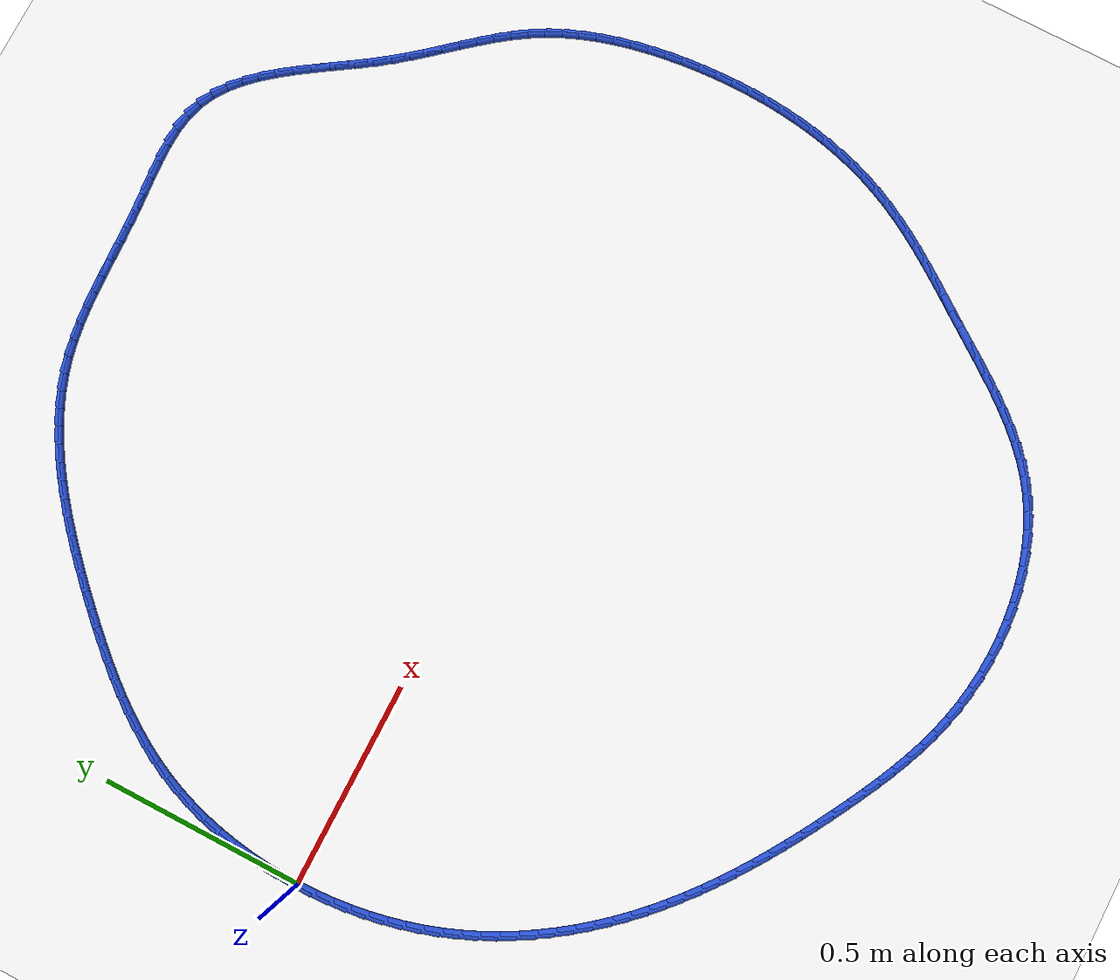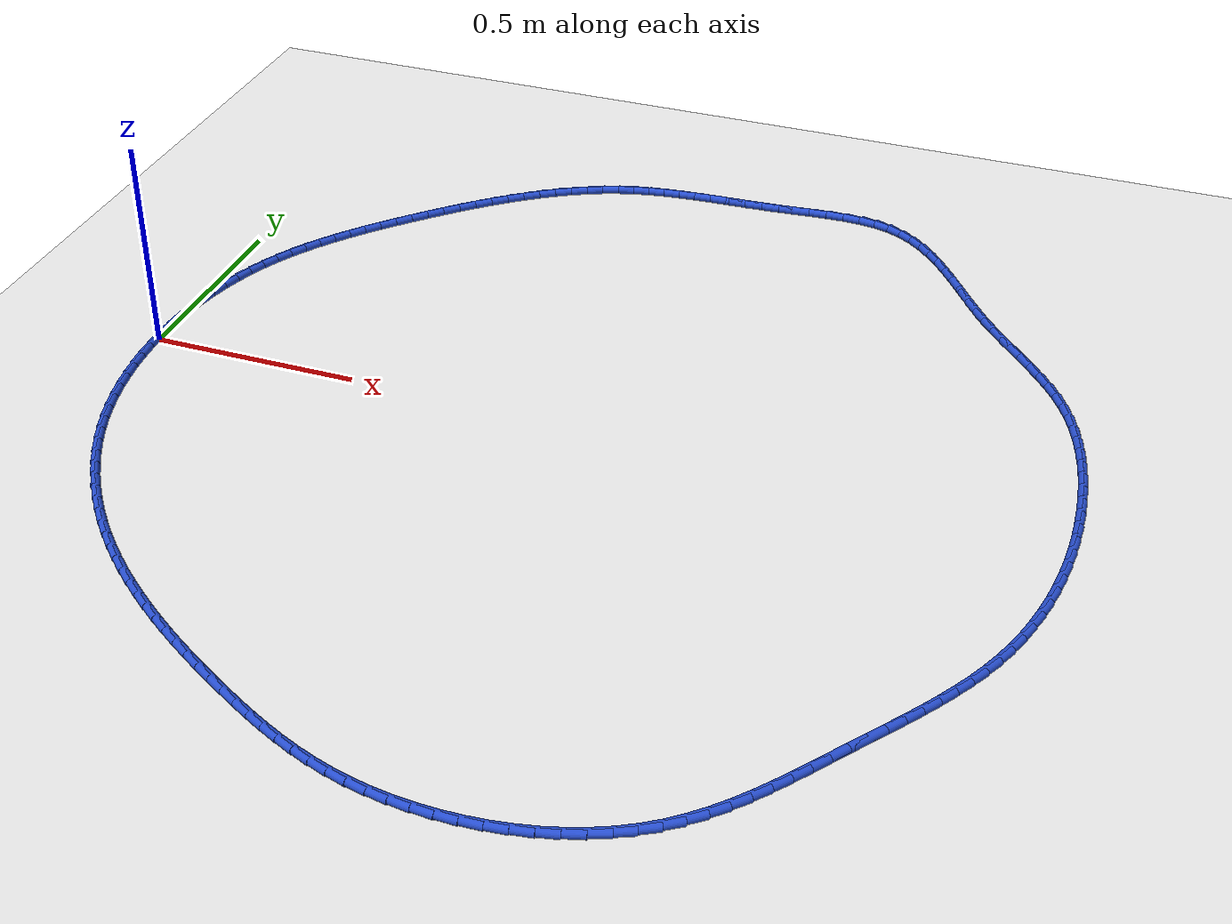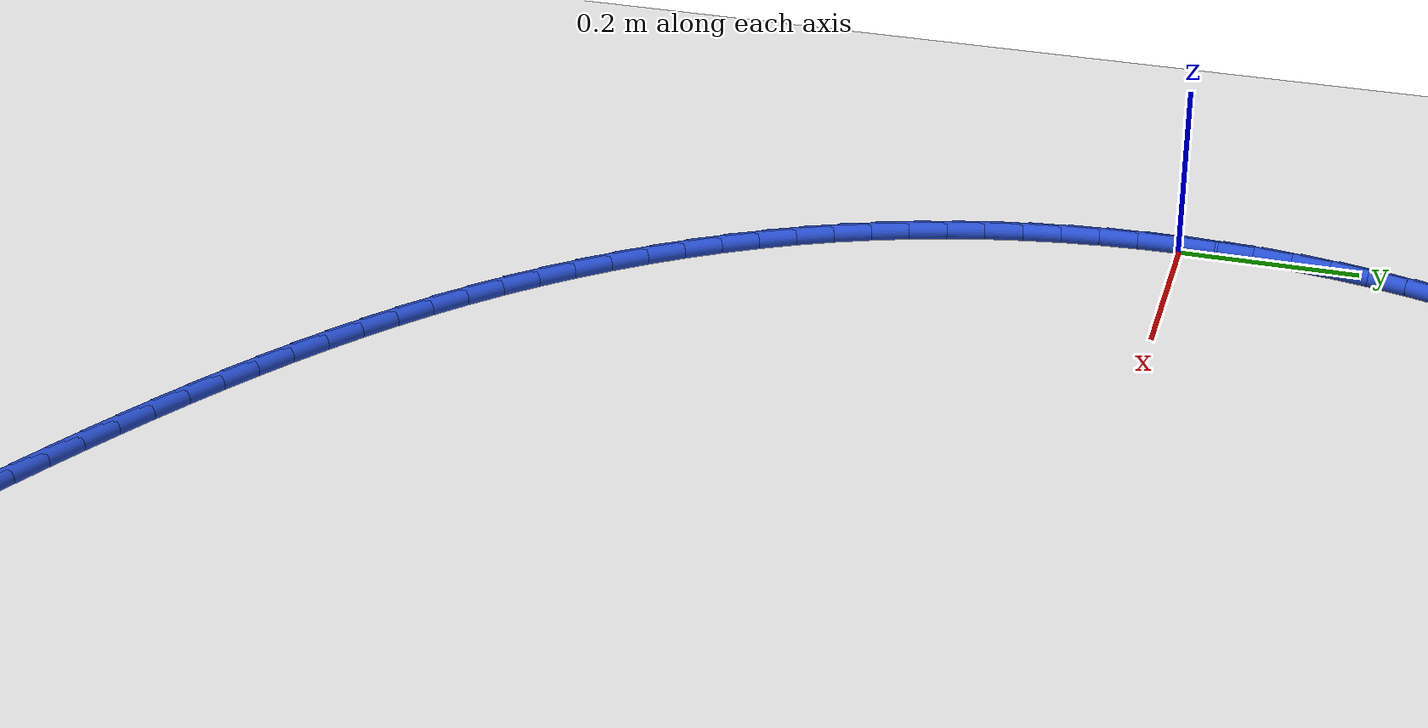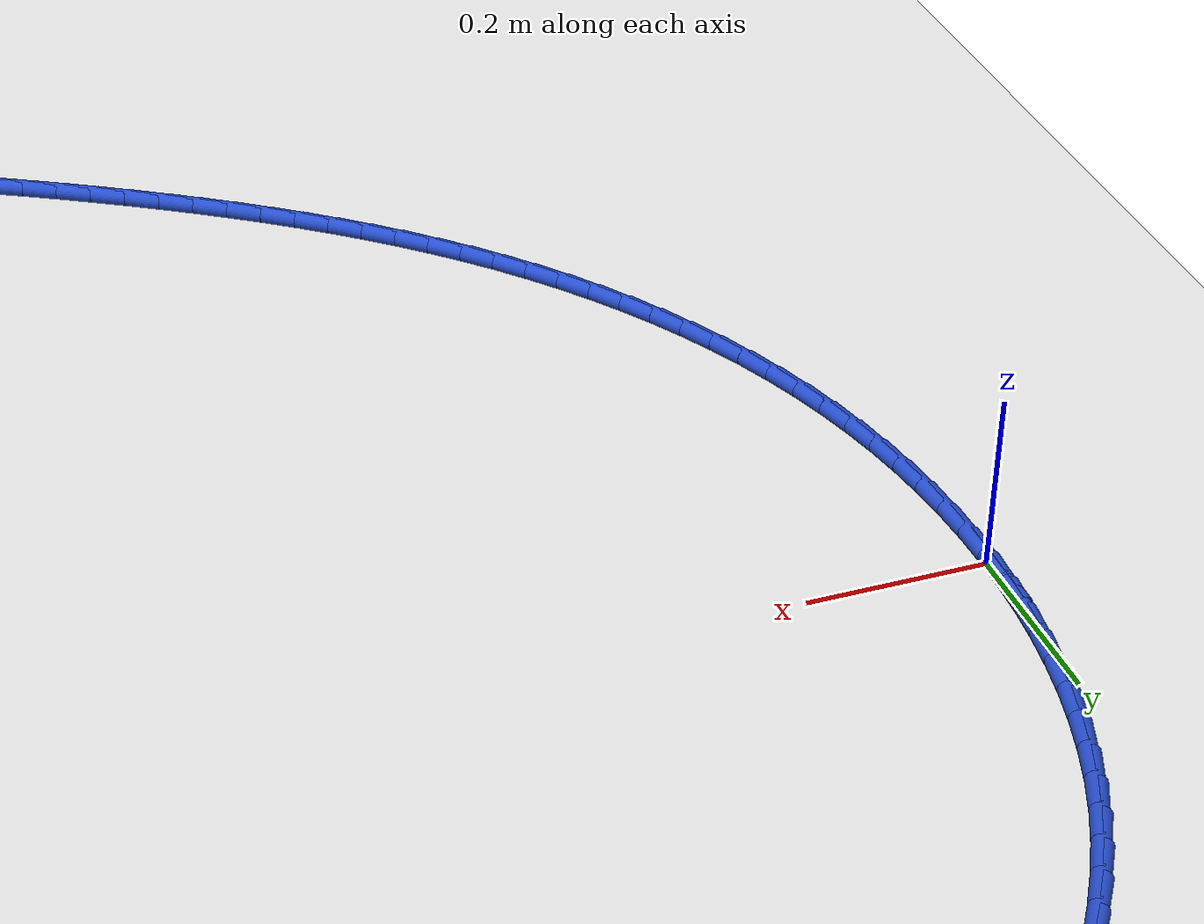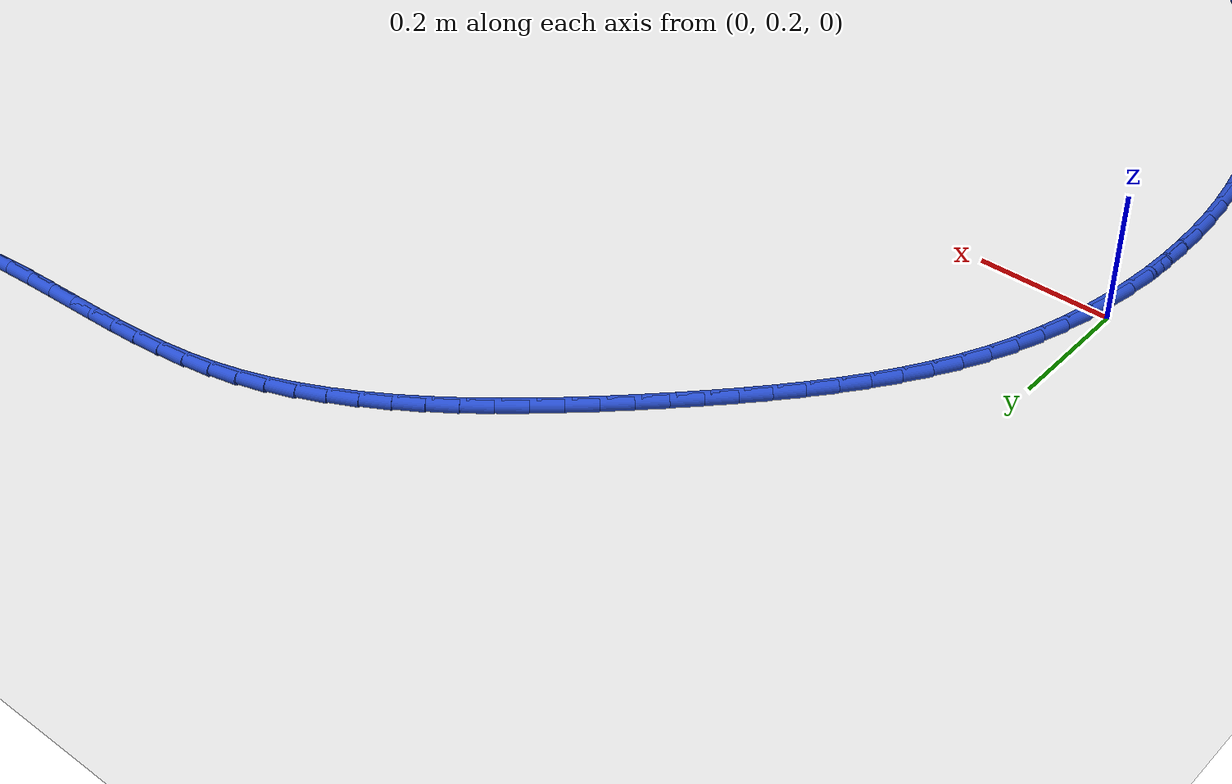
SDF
<sdf version="1.6">
 <world name="default">
  <light name="sun" type="directional">
   <pose>0 0 10 0 -0 0</pose>
   <diffuse>0.8 0.8 0.8 1</diffuse>
   <specular>0.2 0.2 0.2 1</specular>
   <attenuation>
    <range>1000</range>
    <constant>0.9</constant>
    <linear>0.01</linear>
    <quadratic>0.001</quadratic>
   </attenuation>
   <direction>-0.5 0.1 -0.9</direction>
  </light>
  <model name="ground_plane">
   <static>1</static>
   <link name="link">
    <collision name="collision">
     <geometry><plane><normal>0 0 1</normal><size>100 100</size></plane></geometry>
     <surface><friction><ode><mu>100</mu><mu2>50</mu2></ode></friction></surface>
    </collision>
    <visual name="visual">
     <cast_shadows>0</cast_shadows>
     <geometry><plane><normal>0 0 1</normal><size>100 100</size></plane></geometry>
     <material>
      <script><uri>file://media/materials/scripts/gazebo.material</uri><name>Gazebo/WhiteGlow</name></script>
     </material>
    </visual>
   </link>
  </model>
  <gravity>0 0 -9.8</gravity>
  <magnetic_field>6e-06 2.3e-05 -4.2e-05</magnetic_field>
  <atmosphere type="adiabatic"/>
  <physics name="default_physics" default="0" type="ode">
   <max_step_size>0.001</max_step_size>
   <real_time_factor>1</real_time_factor>
   <real_time_update_rate>1000</real_time_update_rate>
  </physics>
  <scene><ambient>0.4 0.4 0.4 1</ambient><background>0.7 0.7 0.7 1</background><shadows>1</shadows></scene>
  <spherical_coordinates>
   <surface_model>EARTH_WGS84</surface_model>
   <latitude_deg>0</latitude_deg>
   <longitude_deg>0</longitude_deg>
   <elevation>0</elevation>
   <heading_deg>0</heading_deg>
  </spherical_coordinates>
  <model name="line">
   <link name="link_0">
    <pose>-1.5612511283791264e-17 -1.3877787807814457e-17 0.01 0 1.57 1.5550382018459732</pose>
    <collision name="collision">
     <geometry><cylinder><radius>0.01</radius><length>0.08</length></cylinder></geometry>
    </collision>
    <visual name="visual">
     <material>
      <script><name>Gazebo/Blue</name><uri>file://media/materials/scripts/gazebo.material</uri></script>
     </material>
     <geometry><cylinder><radius>0.01</radius><length>0.08</length></cylinder></geometry>
    </visual>
   </link>
   <link name="link_1">
    <pose>0.0006871009686475403 0.04359935567451913 0.01 0 1.57 1.513467387537418</pose>
    <collision name="collision">
     <geometry><cylinder><radius>0.01</radius><length>0.08</length></cylinder></geometry>
    </collision>
    <visual name="visual">
     <material>
      <script><name>Gazebo/Blue</name><uri>file://media/materials/scripts/gazebo.material</uri></script>
     </material>
     <geometry><cylinder><radius>0.01</radius><length>0.08</length></cylinder></geometry>
    </visual>
   </link>
   <link name="link_2">
    <pose>0.00318736421278894 0.08716415119225286 0.01 0 1.57 1.470846072998823</pose>
    <collision name="collision">
     <geometry><cylinder><radius>0.01</radius><length>0.08</length></cylinder></geometry>
    </collision>
    <visual name="visual">
     <material>
      <script><name>Gazebo/Blue</name><uri>file://media/materials/scripts/gazebo.material</uri></script>
     </material>
     <geometry><cylinder><radius>0.01</radius><length>0.08</length></cylinder></geometry>
    </visual>
   </link>
   <link name="link_3">
    <pose>0.007538731798664652 0.1305544141502632 0.01 0 1.57 1.4269265725976394</pose>
    <collision name="collision">
     <geometry><cylinder><radius>0.01</radius><length>0.08</length></cylinder></geometry>
    </collision>
    <visual name="visual">
     <material>
      <script><name>Gazebo/Blue</name><uri>file://media/materials/scripts/gazebo.material</uri></script>
     </material>
     <geometry><cylinder><radius>0.01</radius><length>0.08</length></cylinder></geometry>
    </visual>
   </link>
   <link name="link_4">
    <pose>0.013779145792515098 0.1736301721456119 0.01 0 1.57 1.3814642140110918</pose>
    <collision name="collision">
     <geometry><cylinder><radius>0.01</radius><length>0.08</length></cylinder></geometry>
    </collision>
    <visual name="visual">
     <material>
      <script><name>Gazebo/Blue</name><uri>file://media/materials/scripts/gazebo.material</uri></script>
     </material>
     <geometry><cylinder><radius>0.01</radius><length>0.08</length></cylinder></geometry>
    </visual>
   </link>
   <link name="link_5">
    <pose>0.02194654826058074 0.21625145277536093 0.01 0 1.57 1.334219068965814</pose>
    <collision name="collision">
     <geometry><cylinder><radius>0.01</radius><length>0.08</length></cylinder></geometry>
    </collision>
    <visual name="visual">
     <material>
      <script><name>Gazebo/Blue</name><uri>file://media/materials/scripts/gazebo.material</uri></script>
     </material>
     <geometry><cylinder><radius>0.01</radius><length>0.08</length></cylinder></geometry>
    </visual>
   </link>
   <link name="link_6">
    <pose>0.032078881269102036 0.2582782836365722 0.01 0 1.57 1.2849593329055553</pose>
    <collision name="collision">
     <geometry><cylinder><radius>0.01</radius><length>0.08</length></cylinder></geometry>
    </collision>
    <visual name="visual">
     <material>
      <script><name>Gazebo/Blue</name><uri>file://media/materials/scripts/gazebo.material</uri></script>
     </material>
     <geometry><cylinder><radius>0.01</radius><length>0.08</length></cylinder></geometry>
    </visual>
   </link>
   <link name="link_7">
    <pose>0.044214086884319395 0.2995706923263074 0.01 0 1.57 1.2334666904937064</pose>
    <collision name="collision">
     <geometry><cylinder><radius>0.01</radius><length>0.08</length></cylinder></geometry>
    </collision>
    <visual name="visual">
     <material>
      <script><name>Gazebo/Blue</name><uri>file://media/materials/scripts/gazebo.material</uri></script>
     </material>
     <geometry><cylinder><radius>0.01</radius><length>0.08</length></cylinder></geometry>
    </visual>
   </link>
   <link name="link_8">
    <pose>0.058390107172473296 0.3399887064416287 0.01 0 1.57 1.1795439919968023</pose>
    <collision name="collision">
     <geometry><cylinder><radius>0.01</radius><length>0.08</length></cylinder></geometry>
    </collision>
    <visual name="visual">
     <material>
      <script><name>Gazebo/Blue</name><uri>file://media/materials/scripts/gazebo.material</uri></script>
     </material>
     <geometry><cylinder><radius>0.01</radius><length>0.08</length></cylinder></geometry>
    </visual>
   </link>
   <link name="link_9">
    <pose>0.07464488419980417 0.3793923535795977 0.01 0 1.57 1.1238607000228524</pose>
    <collision name="collision">
     <geometry><cylinder><radius>0.01</radius><length>0.08</length></cylinder></geometry>
    </collision>
    <visual name="visual">
     <material>
      <script><name>Gazebo/Blue</name><uri>file://media/materials/scripts/gazebo.material</uri></script>
     </material>
     <geometry><cylinder><radius>0.01</radius><length>0.08</length></cylinder></geometry>
    </visual>
   </link>
   <link name="link_10">
    <pose>0.09299164648599051 0.41767209738841987 0.01 0 1.57 1.0707966860031783</pose>
    <collision name="collision">
     <geometry><cylinder><radius>0.01</radius><length>0.08</length></cylinder></geometry>
    </collision>
    <visual name="visual">
     <material>
      <script><name>Gazebo/Blue</name><uri>file://media/materials/scripts/gazebo.material</uri></script>
     </material>
     <geometry><cylinder><radius>0.01</radius><length>0.08</length></cylinder></geometry>
    </visual>
   </link>
   <link name="link_11">
    <pose>0.11331598915301787 0.4548755888552381 0.01 0 1.57 1.0220733111712463</pose>
    <collision name="collision">
     <geometry><cylinder><radius>0.01</radius><length>0.08</length></cylinder></geometry>
    </collision>
    <visual name="visual">
     <material>
      <script><name>Gazebo/Blue</name><uri>file://media/materials/scripts/gazebo.material</uri></script>
     </material>
     <geometry><cylinder><radius>0.01</radius><length>0.08</length></cylinder></geometry>
    </visual>
   </link>
   <link name="link_12">
    <pose>0.13546242474052025 0.4911010743592577 0.01 0 1.57 0.9779288143758333</pose>
    <collision name="collision">
     <geometry><cylinder><radius>0.01</radius><length>0.08</length></cylinder></geometry>
    </collision>
    <visual name="visual">
     <material>
      <script><name>Gazebo/Blue</name><uri>file://media/materials/scripts/gazebo.material</uri></script>
     </material>
     <geometry><cylinder><radius>0.01</radius><length>0.08</length></cylinder></geometry>
    </visual>
   </link>
   <link name="link_13">
    <pose>0.1592754461132365 0.5264468245103668 0.01 0 1.57 0.9384811509969231</pose>
    <collision name="collision">
     <geometry><cylinder><radius>0.01</radius><length>0.08</length></cylinder></geometry>
    </collision>
    <visual name="visual">
     <material>
      <script><name>Gazebo/Blue</name><uri>file://media/materials/scripts/gazebo.material</uri></script>
     </material>
     <geometry><cylinder><radius>0.01</radius><length>0.08</length></cylinder></geometry>
    </visual>
   </link>
   <link name="link_14">
    <pose>0.1845995461359056 0.5610111099184542 0.01 0 1.57 0.9037546946857914</pose>
    <collision name="collision">
     <geometry><cylinder><radius>0.01</radius><length>0.08</length></cylinder></geometry>
    </collision>
    <visual name="visual">
     <material>
      <script><name>Gazebo/Blue</name><uri>file://media/materials/scripts/gazebo.material</uri></script>
     </material>
     <geometry><cylinder><radius>0.01</radius><length>0.08</length></cylinder></geometry>
    </visual>
   </link>
   <link name="link_15">
    <pose>0.21127921767326646 0.5948922011934078 0.01 0 1.57 0.8737065398478318</pose>
    <collision name="collision">
     <geometry><cylinder><radius>0.01</radius><length>0.08</length></cylinder></geometry>
    </collision>
    <visual name="visual">
     <material>
      <script><name>Gazebo/Blue</name><uri>file://media/materials/scripts/gazebo.material</uri></script>
     </material>
     <geometry><cylinder><radius>0.01</radius><length>0.08</length></cylinder></geometry>
    </visual>
   </link>
   <link name="link_16">
    <pose>0.2391589535900579 0.6281883689451162 0.01 0 1.57 0.8482503411622736</pose>
    <collision name="collision">
     <geometry><cylinder><radius>0.01</radius><length>0.08</length></cylinder></geometry>
    </collision>
    <visual name="visual">
     <material>
      <script><name>Gazebo/Blue</name><uri>file://media/materials/scripts/gazebo.material</uri></script>
     </material>
     <geometry><cylinder><radius>0.01</radius><length>0.08</length></cylinder></geometry>
    </visual>
   </link>
   <link name="link_17">
    <pose>0.268083246751019 0.6609978837834678 0.01 0 1.57 0.827276311440698</pose>
    <collision name="collision">
     <geometry><cylinder><radius>0.01</radius><length>0.08</length></cylinder></geometry>
    </collision>
    <visual name="visual">
     <material>
      <script><name>Gazebo/Blue</name><uri>file://media/materials/scripts/gazebo.material</uri></script>
     </material>
     <geometry><cylinder><radius>0.01</radius><length>0.08</length></cylinder></geometry>
    </visual>
   </link>
   <link name="link_18">
    <pose>0.2978965900208885 0.6934190163183507 0.01 0 1.57 0.8106669940454487</pose>
    <collision name="collision">
     <geometry><cylinder><radius>0.01</radius><length>0.08</length></cylinder></geometry>
    </collision>
    <visual name="visual">
     <material>
      <script><name>Gazebo/Blue</name><uri>file://media/materials/scripts/gazebo.material</uri></script>
     </material>
     <geometry><cylinder><radius>0.01</radius><length>0.08</length></cylinder></geometry>
    </visual>
   </link>
   <link name="link_19">
    <pose>0.3284434762644053 0.7255500371596532 0.01 0 1.57 0.7974725901435652</pose>
    <collision name="collision">
     <geometry><cylinder><radius>0.01</radius><length>0.08</length></cylinder></geometry>
    </collision>
    <visual name="visual">
     <material>
      <script><name>Gazebo/Blue</name><uri>file://media/materials/scripts/gazebo.material</uri></script>
     </material>
     <geometry><cylinder><radius>0.01</radius><length>0.08</length></cylinder></geometry>
    </visual>
   </link>
   <link name="link_20">
    <pose>0.3595875800980895 0.7574554649428401 0.01 0 1.57 0.78277559821944</pose>
    <collision name="collision">
     <geometry><cylinder><radius>0.01</radius><length>0.08</length></cylinder></geometry>
    </collision>
    <visual name="visual">
     <material>
      <script><name>Gazebo/Blue</name><uri>file://media/materials/scripts/gazebo.material</uri></script>
     </material>
     <geometry><cylinder><radius>0.01</radius><length>0.08</length></cylinder></geometry>
    </visual>
   </link>
   <link name="link_21">
    <pose>0.3913031995947468 0.7890051666307971 0.01 0 1.57 0.7647550760589527</pose>
    <collision name="collision">
     <geometry><cylinder><radius>0.01</radius><length>0.08</length></cylinder></geometry>
    </collision>
    <visual name="visual">
     <material>
      <script><name>Gazebo/Blue</name><uri>file://media/materials/scripts/gazebo.material</uri></script>
     </material>
     <geometry><cylinder><radius>0.01</radius><length>0.08</length></cylinder></geometry>
    </visual>
   </link>
   <link name="link_22">
    <pose>0.4236042052773001 0.8199993779900784 0.01 0 1.57 0.7432710913145363</pose>
    <collision name="collision">
     <geometry><cylinder><radius>0.01</radius><length>0.08</length></cylinder></geometry>
    </collision>
    <visual name="visual">
     <material>
      <script><name>Gazebo/Blue</name><uri>file://media/materials/scripts/gazebo.material</uri></script>
     </material>
     <geometry><cylinder><radius>0.01</radius><length>0.08</length></cylinder></geometry>
    </visual>
   </link>
   <link name="link_23">
    <pose>0.45650451761970134 0.8502382468940229 0.01 0 1.57 0.7181422257717694</pose>
    <collision name="collision">
     <geometry><cylinder><radius>0.01</radius><length>0.08</length></cylinder></geometry>
    </collision>
    <visual name="visual">
     <material>
      <script><name>Gazebo/Blue</name><uri>file://media/materials/scripts/gazebo.material</uri></script>
     </material>
     <geometry><cylinder><radius>0.01</radius><length>0.08</length></cylinder></geometry>
    </visual>
   </link>
   <link name="link_24">
    <pose>0.4900180570959021 0.8795219212159696 0.01 0 1.57 0.6891471883845647</pose>
    <collision name="collision">
     <geometry><cylinder><radius>0.01</radius><length>0.08</length></cylinder></geometry>
    </collision>
    <visual name="visual">
     <material>
      <script><name>Gazebo/Blue</name><uri>file://media/materials/scripts/gazebo.material</uri></script>
     </material>
     <geometry><cylinder><radius>0.01</radius><length>0.08</length></cylinder></geometry>
    </visual>
   </link>
   <link name="link_25">
    <pose>0.5241587441798541 0.9076505488292574 0.01 0 1.57 0.6560302871846188</pose>
    <collision name="collision">
     <geometry><cylinder><radius>0.01</radius><length>0.08</length></cylinder></geometry>
    </collision>
    <visual name="visual">
     <material>
      <script><name>Gazebo/Blue</name><uri>file://media/materials/scripts/gazebo.material</uri></script>
     </material>
     <geometry><cylinder><radius>0.01</radius><length>0.08</length></cylinder></geometry>
    </visual>
   </link>
   <link name="link_26">
    <pose>0.5589404993455092 0.9344242776072257 0.01 0 1.57 0.6185098906509917</pose>
    <collision name="collision">
     <geometry><cylinder><radius>0.01</radius><length>0.08</length></cylinder></geometry>
    </collision>
    <visual name="visual">
     <material>
      <script><name>Gazebo/Blue</name><uri>file://media/materials/scripts/gazebo.material</uri></script>
     </material>
     <geometry><cylinder><radius>0.01</radius><length>0.08</length></cylinder></geometry>
    </visual>
   </link>
   <link name="link_27">
    <pose>0.5943772430668193 0.9596432554232133 0.01 0 1.57 0.5762915023212554</pose>
    <collision name="collision">
     <geometry><cylinder><radius>0.01</radius><length>0.08</length></cylinder></geometry>
    </collision>
    <visual name="visual">
     <material>
      <script><name>Gazebo/Blue</name><uri>file://media/materials/scripts/gazebo.material</uri></script>
     </material>
     <geometry><cylinder><radius>0.01</radius><length>0.08</length></cylinder></geometry>
    </visual>
   </link>
   <link name="link_28">
    <pose>0.6304828958177356 0.9831076301505588 0.01 0 1.57 0.5290873310821678</pose>
    <collision name="collision">
     <geometry><cylinder><radius>0.01</radius><length>0.08</length></cylinder></geometry>
    </collision>
    <visual name="visual">
     <material>
      <script><name>Gazebo/Blue</name><uri>file://media/materials/scripts/gazebo.material</uri></script>
     </material>
     <geometry><cylinder><radius>0.01</radius><length>0.08</length></cylinder></geometry>
    </visual>
   </link>
   <link name="link_29">
    <pose>0.6672713780722108 1.0046175496626017 0.01 0 1.57 0.47664425979452857</pose>
    <collision name="collision">
     <geometry><cylinder><radius>0.01</radius><length>0.08</length></cylinder></geometry>
    </collision>
    <visual name="visual">
     <material>
      <script><name>Gazebo/Blue</name><uri>file://media/materials/scripts/gazebo.material</uri></script>
     </material>
     <geometry><cylinder><radius>0.01</radius><length>0.08</length></cylinder></geometry>
    </visual>
   </link>
   <link name="link_30">
    <pose>0.7047566103041952 1.0239731618326802 0.01 0 1.57 0.41878159249070074</pose>
    <collision name="collision">
     <geometry><cylinder><radius>0.01</radius><length>0.08</length></cylinder></geometry>
    </collision>
    <visual name="visual">
     <material>
      <script><name>Gazebo/Blue</name><uri>file://media/materials/scripts/gazebo.material</uri></script>
     </material>
     <geometry><cylinder><radius>0.01</radius><length>0.08</length></cylinder></geometry>
    </visual>
   </link>
   <link name="link_31">
    <pose>0.742952512987642 1.0409746145341343 0.01 0 1.57 0.3554384833448973</pose>
    <collision name="collision">
     <geometry><cylinder><radius>0.01</radius><length>0.08</length></cylinder></geometry>
    </collision>
    <visual name="visual">
     <material>
      <script><name>Gazebo/Blue</name><uri>file://media/materials/scripts/gazebo.material</uri></script>
     </material>
     <geometry><cylinder><radius>0.01</radius><length>0.08</length></cylinder></geometry>
    </visual>
   </link>
   <link name="link_32">
    <pose>0.781873006596502 1.0554220556403022 0.01 0 1.57 0.2868626155793143</pose>
    <collision name="collision">
     <geometry><cylinder><radius>0.01</radius><length>0.08</length></cylinder></geometry>
    </collision>
    <visual name="visual">
     <material>
      <script><name>Gazebo/Blue</name><uri>file://media/materials/scripts/gazebo.material</uri></script>
     </material>
     <geometry><cylinder><radius>0.01</radius><length>0.08</length></cylinder></geometry>
    </visual>
   </link>
   <link name="link_33">
    <pose>0.8215315670307088 1.0671212993282142 0.01 0 1.57 0.21947225379266788</pose>
    <collision name="collision">
     <geometry><cylinder><radius>0.01</radius><length>0.08</length></cylinder></geometry>
    </collision>
    <visual name="visual">
     <material>
      <script><name>Gazebo/Blue</name><uri>file://media/materials/scripts/gazebo.material</uri></script>
     </material>
     <geometry><cylinder><radius>0.01</radius><length>0.08</length></cylinder></geometry>
    </visual>
   </link>
   <link name="link_34">
    <pose>0.8619218349955481 1.07613096860286 0.01 0 1.57 0.16228789919493547</pose>
    <collision name="collision">
     <geometry><cylinder><radius>0.01</radius><length>0.08</length></cylinder></geometry>
    </collision>
    <visual name="visual">
     <material>
      <script><name>Gazebo/Blue</name><uri>file://media/materials/scripts/gazebo.material</uri></script>
     </material>
     <geometry><cylinder><radius>0.01</radius><length>0.08</length></cylinder></geometry>
    </visual>
   </link>
   <link name="link_35">
    <pose>0.9030101023063313 1.082858260856509 0.01 0 1.57 0.11629887673650142</pose>
    <collision name="collision">
     <geometry><cylinder><radius>0.01</radius><length>0.08</length></cylinder></geometry>
    </collision>
    <visual name="visual">
     <material>
      <script><name>Gazebo/Blue</name><uri>file://media/materials/scripts/gazebo.material</uri></script>
     </material>
     <geometry><cylinder><radius>0.01</radius><length>0.08</length></cylinder></geometry>
    </visual>
   </link>
   <link name="link_36">
    <pose>0.9447606646905307 1.0877358145540368 0.01 0 1.57 0.08147769296634808</pose>
    <collision name="collision">
     <geometry><cylinder><radius>0.01</radius><length>0.08</length></cylinder></geometry>
    </collision>
    <visual name="visual">
     <material>
      <script><name>Gazebo/Blue</name><uri>file://media/materials/scripts/gazebo.material</uri></script>
     </material>
     <geometry><cylinder><radius>0.01</radius><length>0.08</length></cylinder></geometry>
    </visual>
   </link>
   <link name="link_37">
    <pose>0.9871378178756175 1.0911962681603193 0.01 0 1.57 0.05756038461225209</pose>
    <collision name="collision">
     <geometry><cylinder><radius>0.01</radius><length>0.08</length></cylinder></geometry>
    </collision>
    <visual name="visual">
     <material>
      <script><name>Gazebo/Blue</name><uri>file://media/materials/scripts/gazebo.material</uri></script>
     </material>
     <geometry><cylinder><radius>0.01</radius><length>0.08</length></cylinder></geometry>
    </visual>
   </link>
   <link name="link_38">
    <pose>1.0301058575890645 1.093672260140233 0.01 0 1.57 0.04418139509721963</pose>
    <collision name="collision">
     <geometry><cylinder><radius>0.01</radius><length>0.08</length></cylinder></geometry>
    </collision>
    <visual name="visual">
     <material>
      <script><name>Gazebo/Blue</name><uri>file://media/materials/scripts/gazebo.material</uri></script>
     </material>
     <geometry><cylinder><radius>0.01</radius><length>0.08</length></cylinder></geometry>
    </visual>
   </link>
   <link name="link_39">
    <pose>1.0736290795583432 1.095596428958653 0.01 0 1.57 0.04095967337707029</pose>
    <collision name="collision">
     <geometry><cylinder><radius>0.01</radius><length>0.08</length></cylinder></geometry>
    </collision>
    <visual name="visual">
     <material>
      <script><name>Gazebo/Blue</name><uri>file://media/materials/scripts/gazebo.material</uri></script>
     </material>
     <geometry><cylinder><radius>0.01</radius><length>0.08</length></cylinder></geometry>
    </visual>
   </link>
   <link name="link_40">
    <pose>1.1176717795109252 1.0974014130804557 0.01 0 1.57 0.04754119221677851</pose>
    <collision name="collision">
     <geometry><cylinder><radius>0.01</radius><length>0.08</length></cylinder></geometry>
    </collision>
    <visual name="visual">
     <material>
      <script><name>Gazebo/Blue</name><uri>file://media/materials/scripts/gazebo.material</uri></script>
     </material>
     <geometry><cylinder><radius>0.01</radius><length>0.08</length></cylinder></geometry>
    </visual>
   </link>
   <link name="link_41">
    <pose>1.1621982531742834 1.0995198509705162 0.01 0 1.57 0.06360633839593538</pose>
    <collision name="collision">
     <geometry><cylinder><radius>0.01</radius><length>0.08</length></cylinder></geometry>
    </collision>
    <visual name="visual">
     <material>
      <script><name>Gazebo/Blue</name><uri>file://media/materials/scripts/gazebo.material</uri></script>
     </material>
     <geometry><cylinder><radius>0.01</radius><length>0.08</length></cylinder></geometry>
    </visual>
   </link>
   <link name="link_42">
    <pose>1.2071727962758887 1.1023843810937113 0.01 0 1.57 0.08432819635410684</pose>
    <collision name="collision">
     <geometry><cylinder><radius>0.01</radius><length>0.08</length></cylinder></geometry>
    </collision>
    <visual name="visual">
     <material>
      <script><name>Gazebo/Blue</name><uri>file://media/materials/scripts/gazebo.material</uri></script>
     </material>
     <geometry><cylinder><radius>0.01</radius><length>0.08</length></cylinder></geometry>
    </visual>
   </link>
   <link name="link_43">
    <pose>1.2524979456584102 1.1062156552082691 0.01 0 1.57 0.08867296946116272</pose>
    <collision name="collision">
     <geometry><cylinder><radius>0.01</radius><length>0.08</length></cylinder></geometry>
    </collision>
    <visual name="visual">
     <material>
      <script><name>Gazebo/Blue</name><uri>file://media/materials/scripts/gazebo.material</uri></script>
     </material>
     <geometry><cylinder><radius>0.01</radius><length>0.08</length></cylinder></geometry>
    </visual>
   </link>
   <link name="link_44">
    <pose>1.2977871826588578 1.110242145163771 0.01 0 1.57 0.07045001302064229</pose>
    <collision name="collision">
     <geometry><cylinder><radius>0.01</radius><length>0.08</length></cylinder></geometry>
    </collision>
    <visual name="visual">
     <material>
      <script><name>Gazebo/Blue</name><uri>file://media/materials/scripts/gazebo.material</uri></script>
     </material>
     <geometry><cylinder><radius>0.01</radius><length>0.08</length></cylinder></geometry>
    </visual>
   </link>
   <link name="link_45">
    <pose>1.3425694920671825 1.1134022893224529 0.01 0 1.57 0.028122232472044078</pose>
    <collision name="collision">
     <geometry><cylinder><radius>0.01</radius><length>0.08</length></cylinder></geometry>
    </collision>
    <visual name="visual">
     <material>
      <script><name>Gazebo/Blue</name><uri>file://media/materials/scripts/gazebo.material</uri></script>
     </material>
     <geometry><cylinder><radius>0.01</radius><length>0.08</length></cylinder></geometry>
    </visual>
   </link>
   <link name="link_46">
    <pose>1.386373848306317 1.1146344904618735 0.01 0 1.57 -0.04146655883906525</pose>
    <collision name="collision">
     <geometry><cylinder><radius>0.01</radius><length>0.08</length></cylinder></geometry>
    </collision>
    <visual name="visual">
     <material>
      <script><name>Gazebo/Blue</name><uri>file://media/materials/scripts/gazebo.material</uri></script>
     </material>
     <geometry><cylinder><radius>0.01</radius><length>0.08</length></cylinder></geometry>
    </visual>
   </link>
   <link name="link_47">
    <pose>1.428729225799194 1.1128771513595894 0.01 0 1.57 -0.1426723983109633</pose>
    <collision name="collision">
     <geometry><cylinder><radius>0.01</radius><length>0.08</length></cylinder></geometry>
    </collision>
    <visual name="visual">
     <material>
      <script><name>Gazebo/Blue</name><uri>file://media/materials/scripts/gazebo.material</uri></script>
     </material>
     <geometry><cylinder><radius>0.01</radius><length>0.08</length></cylinder></geometry>
    </visual>
   </link>
   <link name="link_48">
    <pose>1.4691645989687465 1.1070686747931584 0.01 0 1.57 -0.27953695806055684</pose>
    <collision name="collision">
     <geometry><cylinder><radius>0.01</radius><length>0.08</length></cylinder></geometry>
    </collision>
    <visual name="visual">
     <material>
      <script><name>Gazebo/Blue</name><uri>file://media/materials/scripts/gazebo.material</uri></script>
     </material>
     <geometry><cylinder><radius>0.01</radius><length>0.08</length></cylinder></geometry>
    </visual>
   </link>
   <link name="link_49">
    <pose>1.5072091318293646 1.0961478751152383 0.01 0 1.57 -0.4408919122192127</pose>
    <collision name="collision">
     <geometry><cylinder><radius>0.01</radius><length>0.08</length></cylinder></geometry>
    </collision>
    <visual name="visual">
     <material>
      <script><name>Gazebo/Blue</name><uri>file://media/materials/scripts/gazebo.material</uri></script>
     </material>
     <geometry><cylinder><radius>0.01</radius><length>0.08</length></cylinder></geometry>
    </visual>
   </link>
   <link name="link_50">
    <pose>1.542578369498026 1.0794581725696317 0.01 0 1.57 -0.5877917946363949</pose>
    <collision name="collision">
     <geometry><cylinder><radius>0.01</radius><length>0.08</length></cylinder></geometry>
    </collision>
    <visual name="visual">
     <material>
      <script><name>Gazebo/Blue</name><uri>file://media/materials/scripts/gazebo.material</uri></script>
     </material>
     <geometry><cylinder><radius>0.01</radius><length>0.08</length></cylinder></geometry>
    </visual>
   </link>
   <link name="link_51">
    <pose>1.5755231452521419 1.0575050190662665 0.01 0 1.57 -0.7094978005479948</pose>
    <collision name="collision">
     <geometry><cylinder><radius>0.01</radius><length>0.08</length></cylinder></geometry>
    </collision>
    <visual name="visual">
     <material>
      <script><name>Gazebo/Blue</name><uri>file://media/materials/scripts/gazebo.material</uri></script>
     </material>
     <geometry><cylinder><radius>0.01</radius><length>0.08</length></cylinder></geometry>
    </visual>
   </link>
   <link name="link_52">
    <pose>1.606389795622737 1.031001189996367 0.01 0 1.57 -0.8056868536598677</pose>
    <collision name="collision">
     <geometry><cylinder><radius>0.01</radius><length>0.08</length></cylinder></geometry>
    </collision>
    <visual name="visual">
     <material>
      <script><name>Gazebo/Blue</name><uri>file://media/materials/scripts/gazebo.material</uri></script>
     </material>
     <geometry><cylinder><radius>0.01</radius><length>0.08</length></cylinder></geometry>
    </visual>
   </link>
   <link name="link_53">
    <pose>1.635524657140838 1.000659460751156 0.01 0 1.57 -0.8785254862672629</pose>
    <collision name="collision">
     <geometry><cylinder><radius>0.01</radius><length>0.08</length></cylinder></geometry>
    </collision>
    <visual name="visual">
     <material>
      <script><name>Gazebo/Blue</name><uri>file://media/materials/scripts/gazebo.material</uri></script>
     </material>
     <geometry><cylinder><radius>0.01</radius><length>0.08</length></cylinder></geometry>
    </visual>
   </link>
   <link name="link_54">
    <pose>1.66327406633747 0.9671926067218594 0.01 0 1.57 -0.9308563245846678</pose>
    <collision name="collision">
     <geometry><cylinder><radius>0.01</radius><length>0.08</length></cylinder></geometry>
    </collision>
    <visual name="visual">
     <material>
      <script><name>Gazebo/Blue</name><uri>file://media/materials/scripts/gazebo.material</uri></script>
     </material>
     <geometry><cylinder><radius>0.01</radius><length>0.08</length></cylinder></geometry>
    </visual>
   </link>
   <link name="link_55">
    <pose>1.6899843597436586 0.9313134032996994 0.01 0 1.57 -0.9652258052043879</pose>
    <collision name="collision">
     <geometry><cylinder><radius>0.01</radius><length>0.08</length></cylinder></geometry>
    </collision>
    <visual name="visual">
     <material>
      <script><name>Gazebo/Blue</name><uri>file://media/materials/scripts/gazebo.material</uri></script>
     </material>
     <geometry><cylinder><radius>0.01</radius><length>0.08</length></cylinder></geometry>
    </visual>
   </link>
   <link name="link_56">
    <pose>1.7160018738904295 0.8937346258758999 0.01 0 1.57 -0.9834997732405544</pose>
    <collision name="collision">
     <geometry><cylinder><radius>0.01</radius><length>0.08</length></cylinder></geometry>
    </collision>
    <visual name="visual">
     <material>
      <script><name>Gazebo/Blue</name><uri>file://media/materials/scripts/gazebo.material</uri></script>
     </material>
     <geometry><cylinder><radius>0.01</radius><length>0.08</length></cylinder></geometry>
    </visual>
   </link>
   <link name="link_57">
    <pose>1.741672945308808 0.8551690498416857 0.01 0 1.57 -0.9867630813665804</pose>
    <collision name="collision">
     <geometry><cylinder><radius>0.01</radius><length>0.08</length></cylinder></geometry>
    </collision>
    <visual name="visual">
     <material>
      <script><name>Gazebo/Blue</name><uri>file://media/materials/scripts/gazebo.material</uri></script>
     </material>
     <geometry><cylinder><radius>0.01</radius><length>0.08</length></cylinder></geometry>
    </visual>
   </link>
   <link name="link_58">
    <pose>1.76734391052982 0.8163294505882798 0.01 0 1.57 -0.9753200796416297</pose>
    <collision name="collision">
     <geometry><cylinder><radius>0.01</radius><length>0.08</length></cylinder></geometry>
    </collision>
    <visual name="visual">
     <material>
      <script><name>Gazebo/Blue</name><uri>file://media/materials/scripts/gazebo.material</uri></script>
     </material>
     <geometry><cylinder><radius>0.01</radius><length>0.08</length></cylinder></geometry>
    </visual>
   </link>
   <link name="link_59">
    <pose>1.7933611060844912 0.7779286035069068 0.01 0 1.57 -0.9487179046697646</pose>
    <collision name="collision">
     <geometry><cylinder><radius>0.01</radius><length>0.08</length></cylinder></geometry>
    </collision>
    <visual name="visual">
     <material>
      <script><name>Gazebo/Blue</name><uri>file://media/materials/scripts/gazebo.material</uri></script>
     </material>
     <geometry><cylinder><radius>0.01</radius><length>0.08</length></cylinder></geometry>
    </visual>
   </link>
   <link name="link_60">
    <pose>1.8200708271165047 0.7406792220331275 0.01 0 1.57 -0.9115690121381403</pose>
    <collision name="collision">
     <geometry><cylinder><radius>0.01</radius><length>0.08</length></cylinder></geometry>
    </collision>
    <visual name="visual">
     <material>
      <script><name>Gazebo/Blue</name><uri>file://media/materials/scripts/gazebo.material</uri></script>
     </material>
     <geometry><cylinder><radius>0.01</radius><length>0.08</length></cylinder></geometry>
    </visual>
   </link>
   <link name="link_61">
    <pose>1.847666728279961 0.7050655211732701 0.01 0 1.57 -0.8821551987293187</pose>
    <collision name="collision">
     <geometry><cylinder><radius>0.01</radius><length>0.08</length></cylinder></geometry>
    </collision>
    <visual name="visual">
     <material>
      <script><name>Gazebo/Blue</name><uri>file://media/materials/scripts/gazebo.material</uri></script>
     </material>
     <geometry><cylinder><radius>0.01</radius><length>0.08</length></cylinder></geometry>
    </visual>
   </link>
   <link name="link_62">
    <pose>1.875845834993603 0.6708282762309931 0.01 0 1.57 -0.8649394055414887</pose>
    <collision name="collision">
     <geometry><cylinder><radius>0.01</radius><length>0.08</length></cylinder></geometry>
    </collision>
    <visual name="visual">
     <material>
      <script><name>Gazebo/Blue</name><uri>file://media/materials/scripts/gazebo.material</uri></script>
     </material>
     <geometry><cylinder><radius>0.01</radius><length>0.08</length></cylinder></geometry>
    </visual>
   </link>
   <link name="link_63">
    <pose>1.9042043416007546 0.6375573212858164 0.01 0 1.57 -0.8605368058862686</pose>
    <collision name="collision">
     <geometry><cylinder><radius>0.01</radius><length>0.08</length></cylinder></geometry>
    </collision>
    <visual name="visual">
     <material>
      <script><name>Gazebo/Blue</name><uri>file://media/materials/scripts/gazebo.material</uri></script>
     </material>
     <geometry><cylinder><radius>0.01</radius><length>0.08</length></cylinder></geometry>
    </visual>
   </link>
   <link name="link_64">
    <pose>1.9323384424447432 0.6048424904172628 0.01 0 1.57 -0.8694775144684911</pose>
    <collision name="collision">
     <geometry><cylinder><radius>0.01</radius><length>0.08</length></cylinder></geometry>
    </collision>
    <visual name="visual">
     <material>
      <script><name>Gazebo/Blue</name><uri>file://media/materials/scripts/gazebo.material</uri></script>
     </material>
     <geometry><cylinder><radius>0.01</radius><length>0.08</length></cylinder></geometry>
    </visual>
   </link>
   <link name="link_65">
    <pose>1.9598443318688947 0.5722736177048531 0.01 0 1.57 -0.8922153812034631</pose>
    <collision name="collision">
     <geometry><cylinder><radius>0.01</radius><length>0.08</length></cylinder></geometry>
    </collision>
    <visual name="visual">
     <material>
      <script><name>Gazebo/Blue</name><uri>file://media/materials/scripts/gazebo.material</uri></script>
     </material>
     <geometry><cylinder><radius>0.01</radius><length>0.08</length></cylinder></geometry>
    </visual>
   </link>
   <link name="link_66">
    <pose>1.9863182042165342 0.5394405372281084 0.01 0 1.57 -0.9290651167384616</pose>
    <collision name="collision">
     <geometry><cylinder><radius>0.01</radius><length>0.08</length></cylinder></geometry>
    </collision>
    <visual name="visual">
     <material>
      <script><name>Gazebo/Blue</name><uri>file://media/materials/scripts/gazebo.material</uri></script>
     </material>
     <geometry><cylinder><radius>0.01</radius><length>0.08</length></cylinder></geometry>
    </visual>
   </link>
   <link name="link_67">
    <pose>2.011356253830988 0.5059330830665507 0.01 0 1.57 -0.9800550445598464</pose>
    <collision name="collision">
     <geometry><cylinder><radius>0.01</radius><length>0.08</length></cylinder></geometry>
    </collision>
    <visual name="visual">
     <material>
      <script><name>Gazebo/Blue</name><uri>file://media/materials/scripts/gazebo.material</uri></script>
     </material>
     <geometry><cylinder><radius>0.01</radius><length>0.08</length></cylinder></geometry>
    </visual>
   </link>
   <link name="link_68">
    <pose>2.034554675055582 0.4713410892997009 0.01 0 1.57 -1.0444371889498945</pose>
    <collision name="collision">
     <geometry><cylinder><radius>0.01</radius><length>0.08</length></cylinder></geometry>
    </collision>
    <visual name="visual">
     <material>
      <script><name>Gazebo/Blue</name><uri>file://media/materials/scripts/gazebo.material</uri></script>
     </material>
     <geometry><cylinder><radius>0.01</radius><length>0.08</length></cylinder></geometry>
    </visual>
   </link>
   <link name="link_69">
    <pose>2.055517346094511 0.43526303548655887 0.01 0 1.57 -1.1132340284326134</pose>
    <collision name="collision">
     <geometry><cylinder><radius>0.01</radius><length>0.08</length></cylinder></geometry>
    </collision>
    <visual name="visual">
     <material>
      <script><name>Gazebo/Blue</name><uri>file://media/materials/scripts/gazebo.material</uri></script>
     </material>
     <geometry><cylinder><radius>0.01</radius><length>0.08</length></cylinder></geometry>
    </visual>
   </link>
   <link name="link_70">
    <pose>2.0740824373513442 0.39756101454874704 0.01 0 1.57 -1.1768475800381455</pose>
    <collision name="collision">
     <geometry><cylinder><radius>0.01</radius><length>0.08</length></cylinder></geometry>
    </collision>
    <visual name="visual">
     <material>
      <script><name>Gazebo/Blue</name><uri>file://media/materials/scripts/gazebo.material</uri></script>
     </material>
     <geometry><cylinder><radius>0.01</radius><length>0.08</length></cylinder></geometry>
    </visual>
   </link>
   <link name="link_71">
    <pose>2.0903597052566827 0.35840269384023615 0.01 0 1.57 -1.234916211165615</pose>
    <collision name="collision">
     <geometry><cylinder><radius>0.01</radius><length>0.08</length></cylinder></geometry>
    </collision>
    <visual name="visual">
     <material>
      <script><name>Gazebo/Blue</name><uri>file://media/materials/scripts/gazebo.material</uri></script>
     </material>
     <geometry><cylinder><radius>0.01</radius><length>0.08</length></cylinder></geometry>
    </visual>
   </link>
   <link name="link_72">
    <pose>2.1044740999191043 0.3179728358489908 0.01 0 1.57 -1.2877248448143674</pose>
    <collision name="collision">
     <geometry><cylinder><radius>0.01</radius><length>0.08</length></cylinder></geometry>
    </collision>
    <visual name="visual">
     <material>
      <script><name>Gazebo/Blue</name><uri>file://media/materials/scripts/gazebo.material</uri></script>
     </material>
     <geometry><cylinder><radius>0.01</radius><length>0.08</length></cylinder></geometry>
    </visual>
   </link>
   <link name="link_73">
    <pose>2.1165505714471866 0.276456203062974 0.01 0 1.57 -1.3356297927896514</pose>
    <collision name="collision">
     <geometry><cylinder><radius>0.01</radius><length>0.08</length></cylinder></geometry>
    </collision>
    <visual name="visual">
     <material>
      <script><name>Gazebo/Blue</name><uri>file://media/materials/scripts/gazebo.material</uri></script>
     </material>
     <geometry><cylinder><radius>0.01</radius><length>0.08</length></cylinder></geometry>
    </visual>
   </link>
   <link name="link_74">
    <pose>2.126714069949507 0.2340375579701506 0.01 0 1.57 -1.3790177093501597</pose>
    <collision name="collision">
     <geometry><cylinder><radius>0.01</radius><length>0.08</length></cylinder></geometry>
    </collision>
    <visual name="visual">
     <material>
      <script><name>Gazebo/Blue</name><uri>file://media/materials/scripts/gazebo.material</uri></script>
     </material>
     <geometry><cylinder><radius>0.01</radius><length>0.08</length></cylinder></geometry>
    </visual>
   </link>
   <link name="link_75">
    <pose>2.1350895455346417 0.19090166305848405 0.01 0 1.57 -1.418276970176401</pose>
    <collision name="collision">
     <geometry><cylinder><radius>0.01</radius><length>0.08</length></cylinder></geometry>
    </collision>
    <visual name="visual">
     <material>
      <script><name>Gazebo/Blue</name><uri>file://media/materials/scripts/gazebo.material</uri></script>
     </material>
     <geometry><cylinder><radius>0.01</radius><length>0.08</length></cylinder></geometry>
    </visual>
   </link>
   <link name="link_76">
    <pose>2.1418019483111697 0.14723328081593776 0.01 0 1.57 -1.4537791335347714</pose>
    <collision name="collision">
     <geometry><cylinder><radius>0.01</radius><length>0.08</length></cylinder></geometry>
    </collision>
    <visual name="visual">
     <material>
      <script><name>Gazebo/Blue</name><uri>file://media/materials/scripts/gazebo.material</uri></script>
     </material>
     <geometry><cylinder><radius>0.01</radius><length>0.08</length></cylinder></geometry>
    </visual>
   </link>
   <link name="link_77">
    <pose>2.1469762283876674 0.10321717373047656 0.01 0 1.57 -1.486125176290463</pose>
    <collision name="collision">
     <geometry><cylinder><radius>0.01</radius><length>0.08</length></cylinder></geometry>
    </collision>
    <visual name="visual">
     <material>
      <script><name>Gazebo/Blue</name><uri>file://media/materials/scripts/gazebo.material</uri></script>
     </material>
     <geometry><cylinder><radius>0.01</radius><length>0.08</length></cylinder></geometry>
    </visual>
   </link>
   <link name="link_78">
    <pose>2.1507264294702257 0.05903170100693177 0.01 0 1.57 -1.518012006115695</pose>
    <collision name="collision">
     <geometry><cylinder><radius>0.01</radius><length>0.08</length></cylinder></geometry>
    </collision>
    <visual name="visual">
     <material>
      <script><name>Gazebo/Blue</name><uri>file://media/materials/scripts/gazebo.material</uri></script>
     </material>
     <geometry><cylinder><radius>0.01</radius><length>0.08</length></cylinder></geometry>
    </visual>
   </link>
   <link name="link_79">
    <pose>2.153063617250014 0.014794762190166686 0.01 0 1.57 -1.550922824705998</pose>
    <collision name="collision">
     <geometry><cylinder><radius>0.01</radius><length>0.08</length></cylinder></geometry>
    </collision>
    <visual name="visual">
     <material>
      <script><name>Gazebo/Blue</name><uri>file://media/materials/scripts/gazebo.material</uri></script>
     </material>
     <geometry><cylinder><radius>0.01</radius><length>0.08</length></cylinder></geometry>
    </visual>
   </link>
   <link name="link_80">
    <pose>2.1539422164387503 -0.02940899779110692 0.01 0 1.57 1.5565943990553839</pose>
    <collision name="collision">
     <geometry><cylinder><radius>0.01</radius><length>0.08</length></cylinder></geometry>
    </collision>
    <visual name="visual">
     <material>
      <script><name>Gazebo/Blue</name><uri>file://media/materials/scripts/gazebo.material</uri></script>
     </material>
     <geometry><cylinder><radius>0.01</radius><length>0.08</length></cylinder></geometry>
    </visual>
   </link>
   <link name="link_81">
    <pose>2.153316064161116 -0.07349527898775675 0.01 0 1.57 1.5212279559447406</pose>
    <collision name="collision">
     <geometry><cylinder><radius>0.01</radius><length>0.08</length></cylinder></geometry>
    </collision>
    <visual name="visual">
     <material>
      <script><name>Gazebo/Blue</name><uri>file://media/materials/scripts/gazebo.material</uri></script>
     </material>
     <geometry><cylinder><radius>0.01</radius><length>0.08</length></cylinder></geometry>
    </visual>
   </link>
   <link name="link_82">
    <pose>2.1511389975417945 -0.11737978145065128 0.01 0 1.57 1.4844455310675044</pose>
    <collision name="collision">
     <geometry><cylinder><radius>0.01</radius><length>0.08</length></cylinder></geometry>
    </collision>
    <visual name="visual">
     <material>
      <script><name>Gazebo/Blue</name><uri>file://media/materials/scripts/gazebo.material</uri></script>
     </material>
     <geometry><cylinder><radius>0.01</radius><length>0.08</length></cylinder></geometry>
    </visual>
   </link>
   <link name="link_83">
    <pose>2.1473648537054677 -0.16097820523065665 0.01 0 1.57 1.446125235773089</pose>
    <collision name="collision">
     <geometry><cylinder><radius>0.01</radius><length>0.08</length></cylinder></geometry>
    </collision>
    <visual name="visual">
     <material>
      <script><name>Gazebo/Blue</name><uri>file://media/materials/scripts/gazebo.material</uri></script>
     </material>
     <geometry><cylinder><radius>0.01</radius><length>0.08</length></cylinder></geometry>
    </visual>
   </link>
   <link name="link_84">
    <pose>2.1419474697768175 -0.20420625037864135 0.01 0 1.57 1.406150575232681</pose>
    <collision name="collision">
     <geometry><cylinder><radius>0.01</radius><length>0.08</length></cylinder></geometry>
    </collision>
    <visual name="visual">
     <material>
      <script><name>Gazebo/Blue</name><uri>file://media/materials/scripts/gazebo.material</uri></script>
     </material>
     <geometry><cylinder><radius>0.01</radius><length>0.08</length></cylinder></geometry>
    </visual>
   </link>
   <link name="link_85">
    <pose>2.134840682880527 -0.24697961694547307 0.01 0 1.57 1.3644135216382514</pose>
    <collision name="collision">
     <geometry><cylinder><radius>0.01</radius><length>0.08</length></cylinder></geometry>
    </collision>
    <visual name="visual">
     <material>
      <script><name>Gazebo/Blue</name><uri>file://media/materials/scripts/gazebo.material</uri></script>
     </material>
     <geometry><cylinder><radius>0.01</radius><length>0.08</length></cylinder></geometry>
    </visual>
   </link>
   <link name="link_86">
    <pose>2.1259983301412784 -0.28921400498201955 0.01 0 1.57 1.3208184187432412</pose>
    <collision name="collision">
     <geometry><cylinder><radius>0.01</radius><length>0.08</length></cylinder></geometry>
    </collision>
    <visual name="visual">
     <material>
      <script><name>Gazebo/Blue</name><uri>file://media/materials/scripts/gazebo.material</uri></script>
     </material>
     <geometry><cylinder><radius>0.01</radius><length>0.08</length></cylinder></geometry>
    </visual>
   </link>
   <link name="link_87">
    <pose>2.115374248683754 -0.3308251145391491 0.01 0 1.57 1.2752867483530825</pose>
    <collision name="collision">
     <geometry><cylinder><radius>0.01</radius><length>0.08</length></cylinder></geometry>
    </collision>
    <visual name="visual">
     <material>
      <script><name>Gazebo/Blue</name><uri>file://media/materials/scripts/gazebo.material</uri></script>
     </material>
     <geometry><cylinder><radius>0.01</radius><length>0.08</length></cylinder></geometry>
    </visual>
   </link>
   <link name="link_88">
    <pose>2.1029222756326362 -0.3717286456677281 0.01 0 1.57 1.2277627186690123</pose>
    <collision name="collision">
     <geometry><cylinder><radius>0.01</radius><length>0.08</length></cylinder></geometry>
    </collision>
    <visual name="visual">
     <material>
      <script><name>Gazebo/Blue</name><uri>file://media/materials/scripts/gazebo.material</uri></script>
     </material>
     <geometry><cylinder><radius>0.01</radius><length>0.08</length></cylinder></geometry>
    </visual>
   </link>
   <link name="link_89">
    <pose>2.0885962481126077 -0.4118402984186248 0.01 0 1.57 1.178219529047844</pose>
    <collision name="collision">
     <geometry><cylinder><radius>0.01</radius><length>0.08</length></cylinder></geometry>
    </collision>
    <visual name="visual">
     <material>
      <script><name>Gazebo/Blue</name><uri>file://media/materials/scripts/gazebo.material</uri></script>
     </material>
     <geometry><cylinder><radius>0.01</radius><length>0.08</length></cylinder></geometry>
    </visual>
   </link>
   <link name="link_90">
    <pose>2.07235000324835 -0.45107577284270717 0.01 0 1.57 1.126972777378681</pose>
    <collision name="collision">
     <geometry><cylinder><radius>0.01</radius><length>0.08</length></cylinder></geometry>
    </collision>
    <visual name="visual">
     <material>
      <script><name>Gazebo/Blue</name><uri>file://media/materials/scripts/gazebo.material</uri></script>
     </material>
     <geometry><cylinder><radius>0.01</radius><length>0.08</length></cylinder></geometry>
    </visual>
   </link>
   <link name="link_91">
    <pose>2.054147837860722 -0.4893590505294075 0.01 0 1.57 1.0787356138030832</pose>
    <collision name="collision">
     <geometry><cylinder><radius>0.01</radius><length>0.08</length></cylinder></geometry>
    </collision>
    <visual name="visual">
     <material>
      <script><name>Gazebo/Blue</name><uri>file://media/materials/scripts/gazebo.material</uri></script>
     </material>
     <geometry><cylinder><radius>0.01</radius><length>0.08</length></cylinder></geometry>
    </visual>
   </link>
   <link name="link_92">
    <pose>2.0341110664331055 -0.5267384329151077 0.01 0 1.57 1.0372902091825713</pose>
    <collision name="collision">
     <geometry><cylinder><radius>0.01</radius><length>0.08</length></cylinder></geometry>
    </collision>
    <visual name="visual">
     <material>
      <script><name>Gazebo/Blue</name><uri>file://media/materials/scripts/gazebo.material</uri></script>
     </material>
     <geometry><cylinder><radius>0.01</radius><length>0.08</length></cylinder></geometry>
    </visual>
   </link>
   <link name="link_93">
    <pose>2.01248213712991 -0.563358129886504 0.01 0 1.57 1.0028394556459574</pose>
    <collision name="collision">
     <geometry><cylinder><radius>0.01</radius><length>0.08</length></cylinder></geometry>
    </collision>
    <visual name="visual">
     <material>
      <script><name>Gazebo/Blue</name><uri>file://media/materials/scripts/gazebo.material</uri></script>
     </material>
     <geometry><cylinder><radius>0.01</radius><length>0.08</length></cylinder></geometry>
    </visual>
   </link>
   <link name="link_94">
    <pose>1.9895066292175947 -0.599364830402532 0.01 0 1.57 0.9753718487942138</pose>
    <collision name="collision">
     <geometry><cylinder><radius>0.01</radius><length>0.08</length></cylinder></geometry>
    </collision>
    <visual name="visual">
     <material>
      <script><name>Gazebo/Blue</name><uri>file://media/materials/scripts/gazebo.material</uri></script>
     </material>
     <geometry><cylinder><radius>0.01</radius><length>0.08</length></cylinder></geometry>
    </visual>
   </link>
   <link name="link_95">
    <pose>1.9654301219626213 -0.6349052234221266 0.01 0 1.57 0.9548042492435083</pose>
    <collision name="collision">
     <geometry><cylinder><radius>0.01</radius><length>0.08</length></cylinder></geometry>
    </collision>
    <visual name="visual">
     <material>
      <script><name>Gazebo/Blue</name><uri>file://media/materials/scripts/gazebo.material</uri></script>
     </material>
     <geometry><cylinder><radius>0.01</radius><length>0.08</length></cylinder></geometry>
    </visual>
   </link>
   <link name="link_96">
    <pose>1.9404981946314488 -0.6701259979042231 0.01 0 1.57 0.9410223682051668</pose>
    <collision name="collision">
     <geometry><cylinder><radius>0.01</radius><length>0.08</length></cylinder></geometry>
    </collision>
    <visual name="visual">
     <material>
      <script><name>Gazebo/Blue</name><uri>file://media/materials/scripts/gazebo.material</uri></script>
     </material>
     <geometry><cylinder><radius>0.01</radius><length>0.08</length></cylinder></geometry>
    </visual>
   </link>
   <link name="link_97">
    <pose>1.9149564264905399 -0.705173842807756 0.01 0 1.57 0.9339097418655374</pose>
    <collision name="collision">
     <geometry><cylinder><radius>0.01</radius><length>0.08</length></cylinder></geometry>
    </collision>
    <visual name="visual">
     <material>
      <script><name>Gazebo/Blue</name><uri>file://media/materials/scripts/gazebo.material</uri></script>
     </material>
     <geometry><cylinder><radius>0.01</radius><length>0.08</length></cylinder></geometry>
    </visual>
   </link>
   <link name="link_98">
    <pose>1.8890503968063523 -0.7401954470916596 0.01 0 1.57 0.9333658339766633</pose>
    <collision name="collision">
     <geometry><cylinder><radius>0.01</radius><length>0.08</length></cylinder></geometry>
    </collision>
    <visual name="visual">
     <material>
      <script><name>Gazebo/Blue</name><uri>file://media/materials/scripts/gazebo.material</uri></script>
     </material>
     <geometry><cylinder><radius>0.01</radius><length>0.08</length></cylinder></geometry>
    </visual>
   </link>
   <link name="link_99">
    <pose>1.8630256848453486 -0.7753374997148699 0.01 0 1.57 0.938059829917183</pose>
    <collision name="collision">
     <geometry><cylinder><radius>0.01</radius><length>0.08</length></cylinder></geometry>
    </collision>
    <visual name="visual">
     <material>
      <script><name>Gazebo/Blue</name><uri>file://media/materials/scripts/gazebo.material</uri></script>
     </material>
     <geometry><cylinder><radius>0.01</radius><length>0.08</length></cylinder></geometry>
    </visual>
   </link>
   <link name="link_100">
    <pose>1.837087975409446 -0.8107080186126946 0.01 0 1.57 0.9380481611316303</pose>
    <collision name="collision">
     <geometry><cylinder><radius>0.01</radius><length>0.08</length></cylinder></geometry>
    </collision>
    <visual name="visual">
     <material>
      <script><name>Gazebo/Blue</name><uri>file://media/materials/scripts/gazebo.material</uri></script>
     </material>
     <geometry><cylinder><radius>0.01</radius><length>0.08</length></cylinder></geometry>
    </visual>
   </link>
   <link name="link_101">
    <pose>1.8111272746138838 -0.8461090239312467 0.01 0 1.57 0.9286147634766178</pose>
    <collision name="collision">
     <geometry><cylinder><radius>0.01</radius><length>0.08</length></cylinder></geometry>
    </collision>
    <visual name="visual">
     <material>
      <script><name>Gazebo/Blue</name><uri>file://media/materials/scripts/gazebo.material</uri></script>
     </material>
     <geometry><cylinder><radius>0.01</radius><length>0.08</length></cylinder></geometry>
    </visual>
   </link>
   <link name="link_102">
    <pose>1.784883516066078 -0.881197065572522 0.01 0 1.57 0.909602461871048</pose>
    <collision name="collision">
     <geometry><cylinder><radius>0.01</radius><length>0.08</length></cylinder></geometry>
    </collision>
    <visual name="visual">
     <material>
      <script><name>Gazebo/Blue</name><uri>file://media/materials/scripts/gazebo.material</uri></script>
     </material>
     <geometry><cylinder><radius>0.01</radius><length>0.08</length></cylinder></geometry>
    </visual>
   </link>
   <link name="link_103">
    <pose>1.7580957207706256 -0.9156278088224296 0.01 0 1.57 0.8807507866250059</pose>
    <collision name="collision">
     <geometry><cylinder><radius>0.01</radius><length>0.08</length></cylinder></geometry>
    </collision>
    <visual name="visual">
     <material>
      <script><name>Gazebo/Blue</name><uri>file://media/materials/scripts/gazebo.material</uri></script>
     </material>
     <geometry><cylinder><radius>0.01</radius><length>0.08</length></cylinder></geometry>
    </visual>
   </link>
   <link name="link_104">
    <pose>1.730502909732122 -0.949056918966878 0.01 0 1.57 0.8417137058338278</pose>
    <collision name="collision">
     <geometry><cylinder><radius>0.01</radius><length>0.08</length></cylinder></geometry>
    </collision>
    <visual name="visual">
     <material>
      <script><name>Gazebo/Blue</name><uri>file://media/materials/scripts/gazebo.material</uri></script>
     </material>
     <geometry><cylinder><radius>0.01</radius><length>0.08</length></cylinder></geometry>
    </visual>
   </link>
   <link name="link_105">
    <pose>1.7018441039551653 -0.9811400612917767 0.01 0 1.57 0.7921398563694119</pose>
    <collision name="collision">
     <geometry><cylinder><radius>0.01</radius><length>0.08</length></cylinder></geometry>
    </collision>
    <visual name="visual">
     <material>
      <script><name>Gazebo/Blue</name><uri>file://media/materials/scripts/gazebo.material</uri></script>
     </material>
     <geometry><cylinder><radius>0.01</radius><length>0.08</length></cylinder></geometry>
    </visual>
   </link>
   <link name="link_106">
    <pose>1.6718583244443521 -1.011532901083035 0.01 0 1.57 0.731796530682206</pose>
    <collision name="collision">
     <geometry><cylinder><radius>0.01</radius><length>0.08</length></cylinder></geometry>
    </collision>
    <visual name="visual">
     <material>
      <script><name>Gazebo/Blue</name><uri>file://media/materials/scripts/gazebo.material</uri></script>
     </material>
     <geometry><cylinder><radius>0.01</radius><length>0.08</length></cylinder></geometry>
    </visual>
   </link>
   <link name="link_107">
    <pose>1.6402845922042792 -1.039891103626561 0.01 0 1.57 0.6607415632924256</pose>
    <collision name="collision">
     <geometry><cylinder><radius>0.01</radius><length>0.08</length></cylinder></geometry>
    </collision>
    <visual name="visual">
     <material>
      <script><name>Gazebo/Blue</name><uri>file://media/materials/scripts/gazebo.material</uri></script>
     </material>
     <geometry><cylinder><radius>0.01</radius><length>0.08</length></cylinder></geometry>
    </visual>
   </link>
   <link name="link_108">
    <pose>1.6068619282395435 -1.0658703342082636 0.01 0 1.57 0.5801091418839455</pose>
    <collision name="collision">
     <geometry><cylinder><radius>0.01</radius><length>0.08</length></cylinder></geometry>
    </collision>
    <visual name="visual">
     <material>
      <script><name>Gazebo/Blue</name><uri>file://media/materials/scripts/gazebo.material</uri></script>
     </material>
     <geometry><cylinder><radius>0.01</radius><length>0.08</length></cylinder></geometry>
    </visual>
   </link>
   <link name="link_109">
    <pose>1.5713502826342214 -1.0891419838503946 0.01 0 1.57 0.49858560673774277</pose>
    <collision name="collision">
     <geometry><cylinder><radius>0.01</radius><length>0.08</length></cylinder></geometry>
    </collision>
    <visual name="visual">
     <material>
      <script><name>Gazebo/Blue</name><uri>file://media/materials/scripts/gazebo.material</uri></script>
     </material>
     <geometry><cylinder><radius>0.01</radius><length>0.08</length></cylinder></geometry>
    </visual>
   </link>
   <link name="link_110">
    <pose>1.5337932457419596 -1.1095905658054388 0.01 0 1.57 0.4218780130183422</pose>
    <collision name="collision">
     <geometry><cylinder><radius>0.01</radius><length>0.08</length></cylinder></geometry>
    </collision>
    <visual name="visual">
     <material>
      <script><name>Gazebo/Blue</name><uri>file://media/materials/scripts/gazebo.material</uri></script>
     </material>
     <geometry><cylinder><radius>0.01</radius><length>0.08</length></cylinder></geometry>
    </visual>
   </link>
   <link name="link_111">
    <pose>1.4944385774743585 -1.1272540026834565 0.01 0 1.57 0.34978227985794885</pose>
    <collision name="collision">
     <geometry><cylinder><radius>0.01</radius><length>0.08</length></cylinder></geometry>
    </collision>
    <visual name="visual">
     <material>
      <script><name>Gazebo/Blue</name><uri>file://media/materials/scripts/gazebo.material</uri></script>
     </material>
     <geometry><cylinder><radius>0.01</radius><length>0.08</length></cylinder></geometry>
    </visual>
   </link>
   <link name="link_112">
    <pose>1.453538532213449 -1.1421735941592743 0.01 0 1.57 0.2818425871183967</pose>
    <collision name="collision">
     <geometry><cylinder><radius>0.01</radius><length>0.08</length></cylinder></geometry>
    </collision>
    <visual name="visual">
     <material>
      <script><name>Gazebo/Blue</name><uri>file://media/materials/scripts/gazebo.material</uri></script>
     </material>
     <geometry><cylinder><radius>0.01</radius><length>0.08</length></cylinder></geometry>
    </visual>
   </link>
   <link name="link_113">
    <pose>1.4113453643412568 -1.1543906399077188 0.01 0 1.57 0.21752770559563295</pose>
    <collision name="collision">
     <geometry><cylinder><radius>0.01</radius><length>0.08</length></cylinder></geometry>
    </collision>
    <visual name="visual">
     <material>
      <script><name>Gazebo/Blue</name><uri>file://media/materials/scripts/gazebo.material</uri></script>
     </material>
     <geometry><cylinder><radius>0.01</radius><length>0.08</length></cylinder></geometry>
    </visual>
   </link>
   <link name="link_114">
    <pose>1.3681113282398107 -1.1639464396036179 0.01 0 1.57 0.1562673878199026</pose>
    <collision name="collision">
     <geometry><cylinder><radius>0.01</radius><length>0.08</length></cylinder></geometry>
    </collision>
    <visual name="visual">
     <material>
      <script><name>Gazebo/Blue</name><uri>file://media/materials/scripts/gazebo.material</uri></script>
     </material>
     <geometry><cylinder><radius>0.01</radius><length>0.08</length></cylinder></geometry>
    </visual>
   </link>
   <link name="link_115">
    <pose>1.3240886782911374 -1.170882292921798 0.01 0 1.57 0.09747519188696391</pose>
    <collision name="collision">
     <geometry><cylinder><radius>0.01</radius><length>0.08</length></cylinder></geometry>
    </collision>
    <visual name="visual">
     <material>
      <script><name>Gazebo/Blue</name><uri>file://media/materials/scripts/gazebo.material</uri></script>
     </material>
     <geometry><cylinder><radius>0.01</radius><length>0.08</length></cylinder></geometry>
    </visual>
   </link>
   <link name="link_116">
    <pose>1.279529668877265 -1.1752394995370865 0.01 0 1.57 0.04056055232526023</pose>
    <collision name="collision">
     <geometry><cylinder><radius>0.01</radius><length>0.08</length></cylinder></geometry>
    </collision>
    <visual name="visual">
     <material>
      <script><name>Gazebo/Blue</name><uri>file://media/materials/scripts/gazebo.material</uri></script>
     </material>
     <geometry><cylinder><radius>0.01</radius><length>0.08</length></cylinder></geometry>
    </visual>
   </link>
   <link name="link_117">
    <pose>1.2346865543802223 -1.1770593591243101 0.01 0 1.57 -0.015067122465307161</pose>
    <collision name="collision">
     <geometry><cylinder><radius>0.01</radius><length>0.08</length></cylinder></geometry>
    </collision>
    <visual name="visual">
     <material>
      <script><name>Gazebo/Blue</name><uri>file://media/materials/scripts/gazebo.material</uri></script>
     </material>
     <geometry><cylinder><radius>0.01</radius><length>0.08</length></cylinder></geometry>
    </visual>
   </link>
   <link name="link_118">
    <pose>1.1898115891820369 -1.1763831713582964 0.01 0 1.57 -0.07000001351940568</pose>
    <collision name="collision">
     <geometry><cylinder><radius>0.01</radius><length>0.08</length></cylinder></geometry>
    </collision>
    <visual name="visual">
     <material>
      <script><name>Gazebo/Blue</name><uri>file://media/materials/scripts/gazebo.material</uri></script>
     </material>
     <geometry><cylinder><radius>0.01</radius><length>0.08</length></cylinder></geometry>
    </visual>
   </link>
   <link name="link_119">
    <pose>1.145157027664736 -1.1732522359138717 0.01 0 1.57 -0.12483734636805593</pose>
    <collision name="collision">
     <geometry><cylinder><radius>0.01</radius><length>0.08</length></cylinder></geometry>
    </collision>
    <visual name="visual">
     <material>
      <script><name>Gazebo/Blue</name><uri>file://media/materials/scripts/gazebo.material</uri></script>
     </material>
     <geometry><cylinder><radius>0.01</radius><length>0.08</length></cylinder></geometry>
    </visual>
   </link>
   <link name="link_120">
    <pose>1.100975124210348 -1.1677078524658633 0.01 0 1.57 -0.18019340893893562</pose>
    <collision name="collision">
     <geometry><cylinder><radius>0.01</radius><length>0.08</length></cylinder></geometry>
    </collision>
    <visual name="visual">
     <material>
      <script><name>Gazebo/Blue</name><uri>file://media/materials/scripts/gazebo.material</uri></script>
     </material>
     <geometry><cylinder><radius>0.01</radius><length>0.08</length></cylinder></geometry>
    </visual>
   </link>
   <link name="link_121">
    <pose>1.0575181332008994 -1.159791320689098 0.01 0 1.57 -0.23642684077281614</pose>
    <collision name="collision">
     <geometry><cylinder><radius>0.01</radius><length>0.08</length></cylinder></geometry>
    </collision>
    <visual name="visual">
     <material>
      <script><name>Gazebo/Blue</name><uri>file://media/materials/scripts/gazebo.material</uri></script>
     </material>
     <geometry><cylinder><radius>0.01</radius><length>0.08</length></cylinder></geometry>
    </visual>
   </link>
   <link name="link_122">
    <pose>1.0150219608230429 -1.1495525966421423 0.01 0 1.57 -0.2903714450896837</pose>
    <collision name="collision">
     <geometry><cylinder><radius>0.01</radius><length>0.08</length></cylinder></geometry>
    </collision>
    <visual name="visual">
     <material>
      <script><name>Gazebo/Blue</name><uri>file://media/materials/scripts/gazebo.material</uri></script>
     </material>
     <geometry><cylinder><radius>0.01</radius><length>0.08</length></cylinder></geometry>
    </visual>
   </link>
   <link name="link_123">
    <pose>0.973517316008744 -1.1371502885092457 0.01 0 1.57 -0.33920230906633153</pose>
    <collision name="collision">
     <geometry><cylinder><radius>0.01</radius><length>0.08</length></cylinder></geometry>
    </collision>
    <visual name="visual">
     <material>
      <script><name>Gazebo/Blue</name><uri>file://media/materials/scripts/gazebo.material</uri></script>
     </material>
     <geometry><cylinder><radius>0.01</radius><length>0.08</length></cylinder></geometry>
    </visual>
   </link>
   <link name="link_124">
    <pose>0.9328949546263744 -1.1228171097441382 0.01 0 1.57 -0.38243227640335964</pose>
    <collision name="collision">
     <geometry><cylinder><radius>0.01</radius><length>0.08</length></cylinder></geometry>
    </collision>
    <visual name="visual">
     <material>
      <script><name>Gazebo/Blue</name><uri>file://media/materials/scripts/gazebo.material</uri></script>
     </material>
     <geometry><cylinder><radius>0.01</radius><length>0.08</length></cylinder></geometry>
    </visual>
   </link>
   <link name="link_125">
    <pose>0.8930429351510171 -1.1067872020726555 0.01 0 1.57 -0.41978088795872825</pose>
    <collision name="collision">
     <geometry><cylinder><radius>0.01</radius><length>0.08</length></cylinder></geometry>
    </collision>
    <visual name="visual">
     <material>
      <script><name>Gazebo/Blue</name><uri>file://media/materials/scripts/gazebo.material</uri></script>
     </material>
     <geometry><cylinder><radius>0.01</radius><length>0.08</length></cylinder></geometry>
    </visual>
   </link>
   <link name="link_126">
    <pose>0.8538493160577545 -1.0892947072206318 0.01 0 1.57 -0.45109526773352976</pose>
    <collision name="collision">
     <geometry><cylinder><radius>0.01</radius><length>0.08</length></cylinder></geometry>
    </collision>
    <visual name="visual">
     <material>
      <script><name>Gazebo/Blue</name><uri>file://media/materials/scripts/gazebo.material</uri></script>
     </material>
     <geometry><cylinder><radius>0.01</radius><length>0.08</length></cylinder></geometry>
    </visual>
   </link>
   <link name="link_127">
    <pose>0.8152021558216704 -1.0705737669139022 0.01 0 1.57 -0.47631427556176587</pose>
    <collision name="collision">
     <geometry><cylinder><radius>0.01</radius><length>0.08</length></cylinder></geometry>
    </collision>
    <visual name="visual">
     <material>
      <script><name>Gazebo/Blue</name><uri>file://media/materials/scripts/gazebo.material</uri></script>
     </material>
     <geometry><cylinder><radius>0.01</radius><length>0.08</length></cylinder></geometry>
    </visual>
   </link>
   <link name="link_128">
    <pose>0.7769895129178471 -1.0508585228783016 0.01 0 1.57 -0.4954350157832852</pose>
    <collision name="collision">
     <geometry><cylinder><radius>0.01</radius><length>0.08</length></cylinder></geometry>
    </collision>
    <visual name="visual">
     <material>
      <script><name>Gazebo/Blue</name><uri>file://media/materials/scripts/gazebo.material</uri></script>
     </material>
     <geometry><cylinder><radius>0.01</radius><length>0.08</length></cylinder></geometry>
    </visual>
   </link>
   <link name="link_129">
    <pose>0.7390994458213677 -1.030383116839665 0.01 0 1.57 -0.5090507570775925</pose>
    <collision name="collision">
     <geometry><cylinder><radius>0.01</radius><length>0.08</length></cylinder></geometry>
    </collision>
    <visual name="visual">
     <material>
      <script><name>Gazebo/Blue</name><uri>file://media/materials/scripts/gazebo.material</uri></script>
     </material>
     <geometry><cylinder><radius>0.01</radius><length>0.08</length></cylinder></geometry>
    </visual>
   </link>
   <link name="link_130">
    <pose>0.7014330530904215 -1.0093610084017068 0.01 0 1.57 -0.5220389578316589</pose>
    <collision name="collision">
     <geometry><cylinder><radius>0.01</radius><length>0.08</length></cylinder></geometry>
    </collision>
    <visual name="visual">
     <material>
      <script><name>Gazebo/Blue</name><uri>file://media/materials/scripts/gazebo.material</uri></script>
     </material>
     <geometry><cylinder><radius>0.01</radius><length>0.08</length></cylinder></geometry>
    </visual>
   </link>
   <link name="link_131">
    <pose>0.6640030809856783 -0.9878285792002847 0.01 0 1.57 -0.536883725411235</pose>
    <collision name="collision">
     <geometry><cylinder><radius>0.01</radius><length>0.08</length></cylinder></geometry>
    </collision>
    <visual name="visual">
     <material>
      <script><name>Gazebo/Blue</name><uri>file://media/materials/scripts/gazebo.material</uri></script>
     </material>
     <geometry><cylinder><radius>0.01</radius><length>0.08</length></cylinder></geometry>
    </visual>
   </link>
   <link name="link_132">
    <pose>0.6268789878773617 -0.965732263072164 0.01 0 1.57 -0.5536289458548418</pose>
    <collision name="collision">
     <geometry><cylinder><radius>0.01</radius><length>0.08</length></cylinder></geometry>
    </collision>
    <visual name="visual">
     <material>
      <script><name>Gazebo/Blue</name><uri>file://media/materials/scripts/gazebo.material</uri></script>
     </material>
     <geometry><cylinder><radius>0.01</radius><length>0.08</length></cylinder></geometry>
    </visual>
   </link>
   <link name="link_133">
    <pose>0.5901306782010814 -0.9430177863755771 0.01 0 1.57 -0.5723019127983296</pose>
    <collision name="collision">
     <geometry><cylinder><radius>0.01</radius><length>0.08</length></cylinder></geometry>
    </collision>
    <visual name="visual">
     <material>
      <script><name>Gazebo/Blue</name><uri>file://media/materials/scripts/gazebo.material</uri></script>
     </material>
     <geometry><cylinder><radius>0.01</radius><length>0.08</length></cylinder></geometry>
    </visual>
   </link>
   <link name="link_134">
    <pose>0.5538280563924484 -0.9196308754687571 0.01 0 1.57 -0.5929309363932004</pose>
    <collision name="collision">
     <geometry><cylinder><radius>0.01</radius><length>0.08</length></cylinder></geometry>
    </collision>
    <visual name="visual">
     <material>
      <script><name>Gazebo/Blue</name><uri>file://media/materials/scripts/gazebo.material</uri></script>
     </material>
     <geometry><cylinder><radius>0.01</radius><length>0.08</length></cylinder></geometry>
    </visual>
   </link>
   <link name="link_135">
    <pose>0.5180410268870729 -0.8955172567099372 0.01 0 1.57 -0.6155432963229088</pose>
    <collision name="collision">
     <geometry><cylinder><radius>0.01</radius><length>0.08</length></cylinder></geometry>
    </collision>
    <visual name="visual">
     <material>
      <script><name>Gazebo/Blue</name><uri>file://media/materials/scripts/gazebo.material</uri></script>
     </material>
     <geometry><cylinder><radius>0.01</radius><length>0.08</length></cylinder></geometry>
    </visual>
   </link>
   <link name="link_136">
    <pose>0.4828394941205652 -0.8706226564573497 0.01 0 1.57 -0.640162868132885</pose>
    <collision name="collision">
     <geometry><cylinder><radius>0.01</radius><length>0.08</length></cylinder></geometry>
    </collision>
    <visual name="visual">
     <material>
      <script><name>Gazebo/Blue</name><uri>file://media/materials/scripts/gazebo.material</uri></script>
     </material>
     <geometry><cylinder><radius>0.01</radius><length>0.08</length></cylinder></geometry>
    </visual>
   </link>
   <link name="link_137">
    <pose>0.44829336252853685 -0.8448928010692286 0.01 0 1.57 -0.6668074056548615</pose>
    <collision name="collision">
     <geometry><cylinder><radius>0.01</radius><length>0.08</length></cylinder></geometry>
    </collision>
    <visual name="visual">
     <material>
      <script><name>Gazebo/Blue</name><uri>file://media/materials/scripts/gazebo.material</uri></script>
     </material>
     <geometry><cylinder><radius>0.01</radius><length>0.08</length></cylinder></geometry>
    </visual>
   </link>
   <link name="link_138">
    <pose>0.41447253654659816 -0.8182734169038067 0.01 0 1.57 -0.6954854859374147</pose>
    <collision name="collision">
     <geometry><cylinder><radius>0.01</radius><length>0.08</length></cylinder></geometry>
    </collision>
    <visual name="visual">
     <material>
      <script><name>Gazebo/Blue</name><uri>file://media/materials/scripts/gazebo.material</uri></script>
     </material>
     <geometry><cylinder><radius>0.01</radius><length>0.08</length></cylinder></geometry>
    </visual>
   </link>
   <link name="link_139">
    <pose>0.3814469206103595 -0.7907102303193164 0.01 0 1.57 -0.7261931569248367</pose>
    <collision name="collision">
     <geometry><cylinder><radius>0.01</radius><length>0.08</length></cylinder></geometry>
    </collision>
    <visual name="visual">
     <material>
      <script><name>Gazebo/Blue</name><uri>file://media/materials/scripts/gazebo.material</uri></script>
     </material>
     <geometry><cylinder><radius>0.01</radius><length>0.08</length></cylinder></geometry>
    </visual>
   </link>
   <link name="link_140">
    <pose>0.34928641915543157 -0.7621489676739918 0.01 0 1.57 -0.7589103727569183</pose>
    <collision name="collision">
     <geometry><cylinder><radius>0.01</radius><length>0.08</length></cylinder></geometry>
    </collision>
    <visual name="visual">
     <material>
      <script><name>Gazebo/Blue</name><uri>file://media/materials/scripts/gazebo.material</uri></script>
     </material>
     <geometry><cylinder><radius>0.01</radius><length>0.08</length></cylinder></geometry>
    </visual>
   </link>
   <link name="link_141">
    <pose>0.3180609366174244 -0.7325353553260645 0.01 0 1.57 -0.7935962641691003</pose>
    <collision name="collision">
     <geometry><cylinder><radius>0.01</radius><length>0.08</length></cylinder></geometry>
    </collision>
    <visual name="visual">
     <material>
      <script><name>Gazebo/Blue</name><uri>file://media/materials/scripts/gazebo.material</uri></script>
     </material>
     <geometry><cylinder><radius>0.01</radius><length>0.08</length></cylinder></geometry>
    </visual>
   </link>
   <link name="link_142">
    <pose>0.2878403907475585 -0.7018152002560271 0.01 0 1.57 -0.8298537381101357</pose>
    <collision name="collision">
     <geometry><cylinder><radius>0.01</radius><length>0.08</length></cylinder></geometry>
    </collision>
    <visual name="visual">
     <material>
      <script><name>Gazebo/Blue</name><uri>file://media/materials/scripts/gazebo.material</uri></script>
     </material>
     <geometry><cylinder><radius>0.01</radius><length>0.08</length></cylinder></geometry>
    </visual>
   </link>
   <link name="link_143">
    <pose>0.258699010501696 -0.6699604125734041 0.01 0 1.57 -0.8668917716151607</pose>
    <collision name="collision">
     <geometry><cylinder><radius>0.01</radius><length>0.08</length></cylinder></geometry>
    </collision>
    <visual name="visual">
     <material>
      <script><name>Gazebo/Blue</name><uri>file://media/materials/scripts/gazebo.material</uri></script>
     </material>
     <geometry><cylinder><radius>0.01</radius><length>0.08</length></cylinder></geometry>
    </visual>
   </link>
   <link name="link_144">
    <pose>0.23072150406305272 -0.6370063511558495 0.01 0 1.57 -0.9047110724543185</pose>
    <collision name="collision">
     <geometry><cylinder><radius>0.01</radius><length>0.08</length></cylinder></geometry>
    </collision>
    <visual name="visual">
     <material>
      <script><name>Gazebo/Blue</name><uri>file://media/materials/scripts/gazebo.material</uri></script>
     </material>
     <geometry><cylinder><radius>0.01</radius><length>0.08</length></cylinder></geometry>
    </visual>
   </link>
   <link name="link_145">
    <pose>0.20399414122696802 -0.6029978300022966 0.01 0 1.57 -0.9434361296710982</pose>
    <collision name="collision">
     <geometry><cylinder><radius>0.01</radius><length>0.08</length></cylinder></geometry>
    </collision>
    <visual name="visual">
     <material>
      <script><name>Gazebo/Blue</name><uri>file://media/materials/scripts/gazebo.material</uri></script>
     </material>
     <geometry><cylinder><radius>0.01</radius><length>0.08</length></cylinder></geometry>
    </visual>
   </link>
   <link name="link_146">
    <pose>0.17860319178878092 -0.5679796631116781 0.01 0 1.57 -0.9831863095261434</pose>
    <collision name="collision">
     <geometry><cylinder><radius>0.01</radius><length>0.08</length></cylinder></geometry>
    </collision>
    <visual name="visual">
     <material>
      <script><name>Gazebo/Blue</name><uri>file://media/materials/scripts/gazebo.material</uri></script>
     </material>
     <geometry><cylinder><radius>0.01</radius><length>0.08</length></cylinder></geometry>
    </visual>
   </link>
   <link name="link_147">
    <pose>0.15463492554383168 -0.5319966644829291 0.01 0 1.57 -1.024074563167116</pose>
    <collision name="collision">
     <geometry><cylinder><radius>0.01</radius><length>0.08</length></cylinder></geometry>
    </collision>
    <visual name="visual">
     <material>
      <script><name>Gazebo/Blue</name><uri>file://media/materials/scripts/gazebo.material</uri></script>
     </material>
     <geometry><cylinder><radius>0.01</radius><length>0.08</length></cylinder></geometry>
    </visual>
   </link>
   <link name="link_148">
    <pose>0.1321756122874592 -0.4950936481149819 0.01 0 1.57 -1.0662056384697898</pose>
    <collision name="collision">
     <geometry><cylinder><radius>0.01</radius><length>0.08</length></cylinder></geometry>
    </collision>
    <visual name="visual">
     <material>
      <script><name>Gazebo/Blue</name><uri>file://media/materials/scripts/gazebo.material</uri></script>
     </material>
     <geometry><cylinder><radius>0.01</radius><length>0.08</length></cylinder></geometry>
    </visual>
   </link>
   <link name="link_149">
    <pose>0.11131152181500296 -0.4573154280067702 0.01 0 1.57 -1.1096737593543151</pose>
    <collision name="collision">
     <geometry><cylinder><radius>0.01</radius><length>0.08</length></cylinder></geometry>
    </collision>
    <visual name="visual">
     <material>
      <script><name>Gazebo/Blue</name><uri>file://media/materials/scripts/gazebo.material</uri></script>
     </material>
     <geometry><cylinder><radius>0.01</radius><length>0.08</length></cylinder></geometry>
    </visual>
   </link>
   <link name="link_150">
    <pose>0.09212892392180232 -0.4187068181572275 0.01 0 1.57 -1.1545595291869868</pose>
    <collision name="collision">
     <geometry><cylinder><radius>0.01</radius><length>0.08</length></cylinder></geometry>
    </collision>
    <visual name="visual">
     <material>
      <script><name>Gazebo/Blue</name><uri>file://media/materials/scripts/gazebo.material</uri></script>
     </material>
     <geometry><cylinder><radius>0.01</radius><length>0.08</length></cylinder></geometry>
    </visual>
   </link>
   <link name="link_151">
    <pose>0.07471407882867183 -0.3793126351628196 0.01 0 1.57 -1.2004484262520667</pose>
    <collision name="collision">
     <geometry><cylinder><radius>0.01</radius><length>0.08</length></cylinder></geometry>
    </collision>
    <visual name="visual">
     <material>
      <script><name>Gazebo/Blue</name><uri>file://media/materials/scripts/gazebo.material</uri></script>
     </material>
     <geometry><cylinder><radius>0.01</radius><length>0.08</length></cylinder></geometry>
    </visual>
   </link>
   <link name="link_152">
    <pose>0.0591332544672378 -0.3391831194547338 0.01 0 1.57 -1.2458858316458354</pose>
    <collision name="collision">
     <geometry><cylinder><radius>0.01</radius><length>0.08</length></cylinder></geometry>
    </collision>
    <visual name="visual">
     <material>
      <script><name>Gazebo/Blue</name><uri>file://media/materials/scripts/gazebo.material</uri></script>
     </material>
     <geometry><cylinder><radius>0.01</radius><length>0.08</length></cylinder></geometry>
    </visual>
   </link>
   <link name="link_153">
    <pose>0.04539060768333605 -0.2983853619738855 0.01 0 1.57 -1.2905990551800772</pose>
    <collision name="collision">
     <geometry><cylinder><radius>0.01</radius><length>0.08</length></cylinder></geometry>
    </collision>
    <visual name="visual">
     <material>
      <script><name>Gazebo/Blue</name><uri>file://media/materials/scripts/gazebo.material</uri></script>
     </material>
     <geometry><cylinder><radius>0.01</radius><length>0.08</length></cylinder></geometry>
    </visual>
   </link>
   <link name="link_154">
    <pose>0.033478268805931764 -0.25698971641110097 0.01 0 1.57 -1.3346123201409377</pose>
    <collision name="collision">
     <geometry><cylinder><radius>0.01</radius><length>0.08</length></cylinder></geometry>
    </collision>
    <visual name="visual">
     <material>
      <script><name>Gazebo/Blue</name><uri>file://media/materials/scripts/gazebo.material</uri></script>
     </material>
     <geometry><cylinder><radius>0.01</radius><length>0.08</length></cylinder></geometry>
    </visual>
   </link>
   <link name="link_155">
    <pose>0.023388368163990047 -0.21506653645720641 0.01 0 1.57 -1.377959338899002</pose>
    <collision name="collision">
     <geometry><cylinder><radius>0.01</radius><length>0.08</length></cylinder></geometry>
    </collision>
    <visual name="visual">
     <material>
      <script><name>Gazebo/Blue</name><uri>file://media/materials/scripts/gazebo.material</uri></script>
     </material>
     <geometry><cylinder><radius>0.01</radius><length>0.08</length></cylinder></geometry>
    </visual>
   </link>
   <link name="link_156">
    <pose>0.015113036086475922 -0.17268617580302728 0.01 0 1.57 -1.4206819143882434</pose>
    <collision name="collision">
     <geometry><cylinder><radius>0.01</radius><length>0.08</length></cylinder></geometry>
    </collision>
    <visual name="visual">
     <material>
      <script><name>Gazebo/Blue</name><uri>file://media/materials/scripts/gazebo.material</uri></script>
     </material>
     <geometry><cylinder><radius>0.01</radius><length>0.08</length></cylinder></geometry>
    </visual>
   </link>
   <link name="link_157">
    <pose>0.008644402902354817 -0.1299189881393913 0.01 0 1.57 -1.4628286101771926</pose>
    <collision name="collision">
     <geometry><cylinder><radius>0.01</radius><length>0.08</length></cylinder></geometry>
    </collision>
    <visual name="visual">
     <material>
      <script><name>Gazebo/Blue</name><uri>file://media/materials/scripts/gazebo.material</uri></script>
     </material>
     <geometry><cylinder><radius>0.01</radius><length>0.08</length></cylinder></geometry>
    </visual>
   </link>
   <link name="link_158">
    <pose>0.003974598940591699 -0.08683532715712394 0.01 0 1.57 -1.5044535133445613</pose>
    <collision name="collision">
     <geometry><cylinder><radius>0.01</radius><length>0.08</length></cylinder></geometry>
    </collision>
    <visual name="visual">
     <material>
      <script><name>Gazebo/Blue</name><uri>file://media/materials/scripts/gazebo.material</uri></script>
     </material>
     <geometry><cylinder><radius>0.01</radius><length>0.08</length></cylinder></geometry>
    </visual>
   </link>
   <link name="link_159">
    <pose>0.0010957545301517064 -0.043505546547051424 0.01 0 1.57 -1.5456151027096463</pose>
    <collision name="collision">
     <geometry><cylinder><radius>0.01</radius><length>0.08</length></cylinder></geometry>
    </collision>
    <visual name="visual">
     <material>
      <script><name>Gazebo/Blue</name><uri>file://media/materials/scripts/gazebo.material</uri></script>
     </material>
     <geometry><cylinder><radius>0.01</radius><length>0.08</length></cylinder></geometry>
    </visual>
   </link>
   <link name="link_160">
    <pose>-2.0816681711721685e-17 1.1102230246251565e-16 0.01 0 1.57 1.5552174281013746</pose>
    <collision name="collision">
     <geometry><cylinder><radius>0.01</radius><length>0.08</length></cylinder></geometry>
    </collision>
    <visual name="visual">
     <material>
      <script><name>Gazebo/Blue</name><uri>file://media/materials/scripts/gazebo.material</uri></script>
     </material>
     <geometry><cylinder><radius>0.01</radius><length>0.08</length></cylinder></geometry>
    </visual>
   </link>
   <link name="link_161">
    <pose>0.0006794656791016696 0.04361095879320516 0.01 0 1.57 1.5552174281013749</pose>
    <collision name="collision">
     <geometry><cylinder><radius>0.01</radius><length>0.08</length></cylinder></geometry>
    </collision>
    <visual name="visual">
     <material>
      <script><name>Gazebo/Blue</name><uri>file://media/materials/scripts/gazebo.material</uri></script>
     </material>
     <geometry><cylinder><radius>0.01</radius><length>0.08</length></cylinder></geometry>
    </visual>
   </link>
  </model>
 </world>
</sdf>
